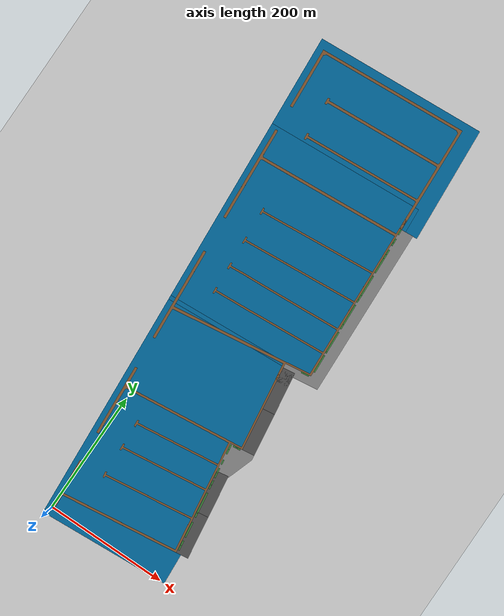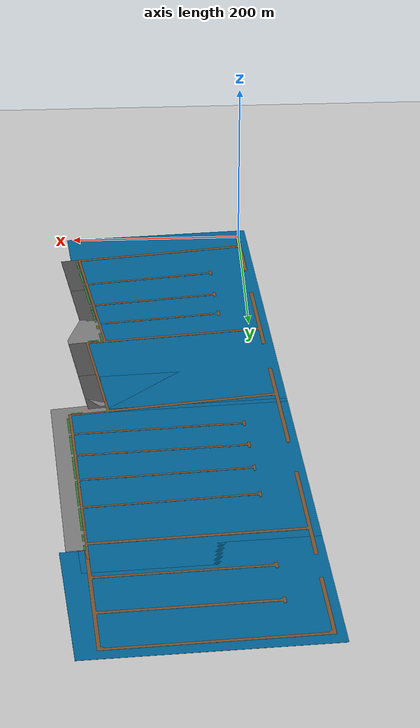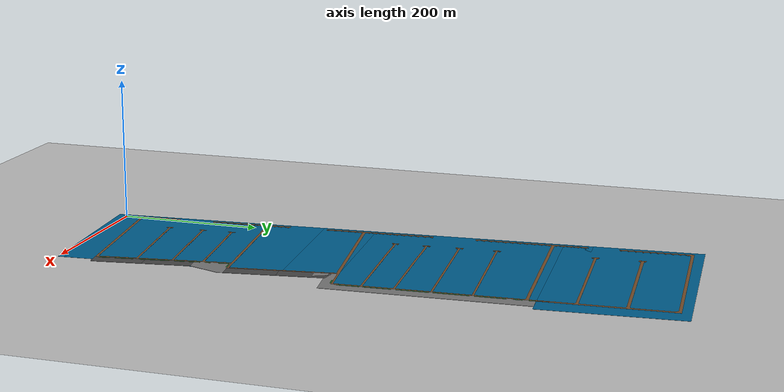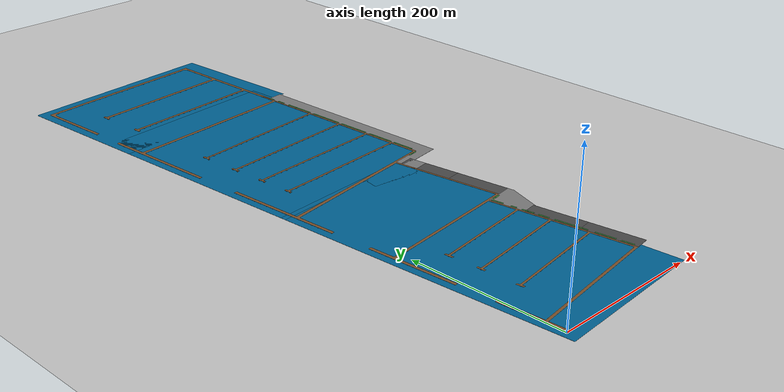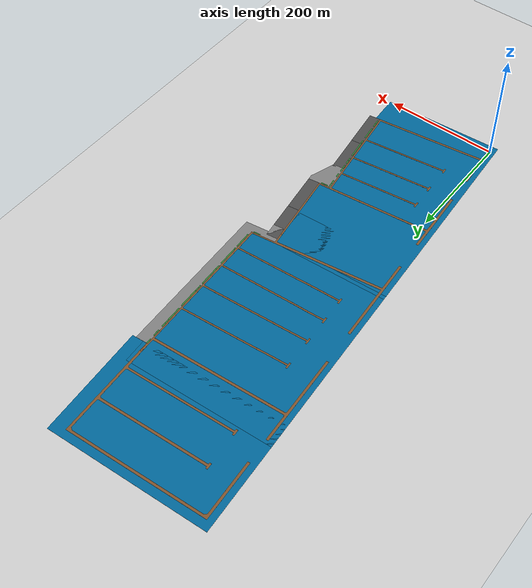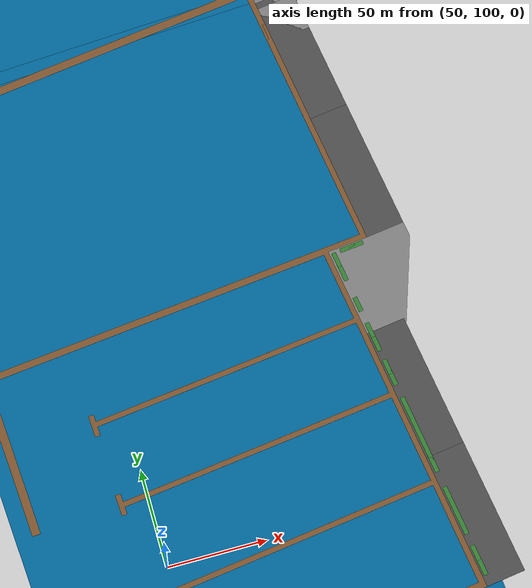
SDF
<sdf version="1.7">
 <world name="marina_base">
  <plugin name="gazebo_ros_state" filename="libgazebo_ros_state.so">
   <ros><namespace>/gazebo</namespace></ros>
   <update_rate>1.0</update_rate>
  </plugin>
  <light name="sun" type="directional">
   <pose>0 0 10 0 -0 0</pose>
   <diffuse>0.8 0.8 0.8 1</diffuse>
   <specular>0.2 0.2 0.2 1</specular>
   <attenuation>
    <range>1000</range>
    <constant>0.9</constant>
    <linear>0.01</linear>
    <quadratic>0.001</quadratic>
   </attenuation>
   <direction>-0.5 0.1 -0.9</direction>
   <spot><inner_angle>0</inner_angle><outer_angle>0</outer_angle><falloff>0</falloff></spot>
  </light>
  <model name="ground_plane">
   <pose>50 50 -1 0 -0 0</pose>
   <static>1</static>
   <link name="link">
    <collision name="collision">
     <geometry><plane><normal>0 0 1</normal><size>100 100</size></plane></geometry>
     <surface><friction><ode><mu>100</mu><mu2>50</mu2></ode></friction></surface>
    </collision>
    <visual name="visual">
     <cast_shadows>0</cast_shadows>
     <geometry><plane><normal>0 0 1</normal><size>100 100</size></plane></geometry>
     <material>
      <script><uri>file://media/materials/scripts/gazebo.material</uri><name>Gazebo/Grey</name></script>
     </material>
    </visual>
   </link>
  </model>
  <gravity>0 0 -9.8</gravity>
  <magnetic_field>6e-06 2.3e-05 -4.2e-05</magnetic_field>
  <atmosphere type="adiabatic"/>
  <physics type="ode">
   <max_step_size>0.001</max_step_size>
   <real_time_factor>1</real_time_factor>
   <real_time_update_rate>1000</real_time_update_rate>
  </physics>
  <scene><ambient>0.4 0.4 0.4 1</ambient><background>0.7 0.7 0.7 1</background><shadows>1</shadows></scene>
  <audio><device>default</device></audio>
  <spherical_coordinates>
   <surface_model>EARTH_WGS84</surface_model>
   <latitude_deg>45.0271</latitude_deg>
   <longitude_deg>14.6258</longitude_deg>
   <elevation>1.5</elevation>
   <heading_deg>180</heading_deg>
  </spherical_coordinates>
  <light name="sun_clone" type="directional">
   <pose>-7.81637 198.095 40 0 -0 0</pose>
   <diffuse>0.8 0.8 0.8 1</diffuse>
   <specular>0.2 0.2 0.2 1</specular>
   <direction>-0.483368 0.096674 -0.870063</direction>
   <attenuation>
    <range>1000</range>
    <constant>0.9</constant>
    <linear>0.01</linear>
    <quadratic>0.001</quadratic>
   </attenuation>
   <cast_shadows>0</cast_shadows>
   <spot><inner_angle>0</inner_angle><outer_angle>0</outer_angle><falloff>0</falloff></spot>
  </light>
  <model name="zone_A">
   <static>1</static>
   <pose>96.71 55.0214 0 0 -0 0.067998</pose>
   <frame name="Marina_Zona_A::__model__" attached_to="Marina_Zona_A::link">
    <pose relative_to="__model__">-100.225 -48.3232 0.08 0 -0 0</pose>
   </frame>
   <link name="Marina_Zona_A::link">
    <inertial>
     <mass>100000</mass>
     <inertia><ixx>0</ixx><ixy>0</ixy><ixz>0</ixz><iyy>0</iyy><iyz>0</iyz><izz>0</izz></inertia>
    </inertial>
    <pose relative_to="Marina_Zona_A::__model__">0 0 0 0 -0 0</pose>
    <visual name="visual">
     <geometry>
      <mesh>
       <uri>/marinero_simulations/models/Marina_Zona_A/meshes/Marina_Zona_A.stl</uri>
       <scale>1 1 1</scale>
      </mesh>
     </geometry>
     <material>
      <script><uri>file://media/materials/scripts/gazebo.material</uri><name>Gazebo/Brown</name></script>
      <ambient>0.278 0.129 0.02 1</ambient>
      <diffuse>0.278 0.129 0.02 1</diffuse>
      <specular>0.278 0.129 0.02 1</specular>
      <emissive>0 0 0 1</emissive>
      <shader type="pixel"><normal_map>__default__</normal_map></shader>
     </material>
    </visual>
    <collision name="collision">
     <geometry>
      <mesh>
       <uri>/marinero_simulations/models/Marina_Zona_A/meshes/Marina_Zona_A.stl</uri>
       <scale>1 1 1</scale>
      </mesh>
     </geometry>
     <surface>
      <friction>
       <ode><mu>1</mu><mu2>1</mu2><fdir1>0 0 0</fdir1><slip1>0.001</slip1><slip2>1e-05</slip2></ode>
       <torsional>
        <coefficient>1</coefficient>
        <patch_radius>0</patch_radius>
        <surface_radius>0</surface_radius>
        <use_patch_radius>1</use_patch_radius>
        <ode><slip>0</slip></ode>
       </torsional>
      </friction>
      <bounce><restitution_coefficient>0</restitution_coefficient><threshold>1000</threshold></bounce>
      <contact>
       <collide_without_contact>0</collide_without_contact>
       <collide_without_contact_bitmask>0</collide_without_contact_bitmask>
       <collide_bitmask>1</collide_bitmask>
       <ode>
        <soft_cfm>0</soft_cfm>
        <soft_erp>0.2</soft_erp>
        <kp>1e+13</kp>
        <kd>10</kd>
        <max_vel>0.01</max_vel>
        <min_depth>0.001</min_depth>
       </ode>
       <bullet>
        <split_impulse>1</split_impulse>
        <split_impulse_penetration_threshold>-0.01</split_impulse_penetration_threshold>
        <soft_cfm>0</soft_cfm>
        <soft_erp>0.2</soft_erp>
        <kp>1e+11</kp>
        <kd>100</kd>
       </bullet>
      </contact>
     </surface>
    </collision>
   </link>
   <static>1</static>
   <frame name="sea_plane_A::__model__" attached_to="sea_plane_A::link">
    <pose relative_to="__model__">-1.12 126.455 0 0 -0 0</pose>
   </frame>
   <link name="sea_plane_A::link">
    <pose relative_to="sea_plane_A::__model__">0 0 0 0 -0 0</pose>
    <inertial>
     <mass>5.27875e+06</mass>
     <inertia>
      <ixx>4.66688e+09</ixx>
      <ixy>0</ixy>
      <ixz>0</ixz>
      <iyy>1.84866e+10</iyy>
      <iyz>0</iyz>
      <izz>2.31535e+10</izz>
     </inertia>
    </inertial>
    <visual name="visual">
     <cast_shadows>0</cast_shadows>
     <geometry><box><size>215 378 0.25</size></box></geometry>
     <material>
      <script>
       <uri>model://sea_plane/materials/scripts</uri>
       <uri>model://sea_plane/materials/textures</uri>
       <name>vrc/sea</name>
      </script>
      <shader type="pixel"><normal_map>__default__</normal_map></shader>
      <ambient>0 0.4 0.6 0</ambient>
      <diffuse>0 0.4 0.6 1</diffuse>
      <specular>0.2 0.2 0.2 1</specular>
      <emissive>0 0 0 1</emissive>
     </material>
    </visual>
    <collision name="collision">
     <geometry><box><size>215 378 0.25</size></box></geometry>
     <surface>
      <friction>
       <ode><mu>1</mu><mu2>1</mu2><fdir1>0 0 0</fdir1><slip1>0</slip1><slip2>0</slip2></ode>
       <torsional>
        <coefficient>1</coefficient>
        <patch_radius>0</patch_radius>
        <surface_radius>0</surface_radius>
        <use_patch_radius>1</use_patch_radius>
        <ode><slip>0</slip></ode>
       </torsional>
      </friction>
      <bounce><restitution_coefficient>0</restitution_coefficient><threshold>1e+06</threshold></bounce>
      <contact>
       <collide_without_contact>0</collide_without_contact>
       <collide_without_contact_bitmask>1</collide_without_contact_bitmask>
       <collide_bitmask>1</collide_bitmask>
       <ode>
        <soft_cfm>0</soft_cfm>
        <soft_erp>0.2</soft_erp>
        <kp>1e+13</kp>
        <kd>1</kd>
        <max_vel>0.01</max_vel>
        <min_depth>0</min_depth>
       </ode>
       <bullet>
        <split_impulse>1</split_impulse>
        <split_impulse_penetration_threshold>-0.01</split_impulse_penetration_threshold>
        <soft_cfm>0</soft_cfm>
        <soft_erp>0.2</soft_erp>
        <kp>1e+13</kp>
        <kd>1</kd>
       </bullet>
      </contact>
     </surface>
    </collision>
   </link>
   <static>1</static>
   <frame name="asphalt_plane_0::__model__" attached_to="asphalt_plane_0::link">
    <pose relative_to="__model__">105.657 22.9966 0 0 0 -1.498</pose>
   </frame>
   <link name="asphalt_plane_0::link">
    <pose relative_to="asphalt_plane_0::__model__">0 0 1.015 0 -0 0</pose>
    <inertial>
     <mass>1</mass>
     <inertia><ixx>1</ixx><ixy>0</ixy><ixz>0</ixz><iyy>1</iyy><iyz>0</iyz><izz>1</izz></inertia>
    </inertial>
    <visual name="visual">
     <cast_shadows>0</cast_shadows>
     <geometry><box><size>70 20 0.5</size></box></geometry>
     <material>
      <script>
       <uri>model://asphalt_plane/materials/scripts</uri>
       <uri>model://asphalt_plane/materials/textures</uri>
       <name>vrc/asphalt</name>
      </script>
      <shader type="pixel"><normal_map>__default__</normal_map></shader>
      <ambient>0.5 0.5 0.5 1</ambient>
      <diffuse>0.5 0.5 0.5 1</diffuse>
      <specular>0.2 0.2 0.2 1</specular>
      <emissive>0 0 0 1</emissive>
     </material>
    </visual>
    <collision name="collision">
     <geometry><box><size>70 20 0.5</size></box></geometry>
     <surface>
      <friction>
       <ode><mu>1</mu><mu2>1</mu2><fdir1>0 0 0</fdir1><slip1>0.001</slip1><slip2>1e-05</slip2></ode>
       <torsional>
        <coefficient>1</coefficient>
        <patch_radius>0</patch_radius>
        <surface_radius>0</surface_radius>
        <use_patch_radius>1</use_patch_radius>
        <ode><slip>0</slip></ode>
       </torsional>
      </friction>
      <bounce><restitution_coefficient>0</restitution_coefficient><threshold>1e+06</threshold></bounce>
      <contact>
       <collide_without_contact>0</collide_without_contact>
       <collide_without_contact_bitmask>1</collide_without_contact_bitmask>
       <collide_bitmask>1</collide_bitmask>
       <ode>
        <soft_cfm>0</soft_cfm>
        <soft_erp>0.2</soft_erp>
        <kp>1e+13</kp>
        <kd>1</kd>
        <max_vel>0.01</max_vel>
        <min_depth>0</min_depth>
       </ode>
       <bullet>
        <split_impulse>1</split_impulse>
        <split_impulse_penetration_threshold>-0.01</split_impulse_penetration_threshold>
        <soft_cfm>0</soft_cfm>
        <soft_erp>0.2</soft_erp>
        <kp>1e+13</kp>
        <kd>1</kd>
       </bullet>
      </contact>
     </surface>
    </collision>
   </link>
   <static>1</static>
   <frame name="asphalt_plane_1::__model__" attached_to="asphalt_plane_1::link">
    <pose relative_to="__model__">100.593 92.427 0 0 0 -1.498</pose>
   </frame>
   <link name="asphalt_plane_1::link">
    <pose relative_to="asphalt_plane_1::__model__">0 0 1.015 0 -0 0</pose>
    <inertial>
     <mass>1</mass>
     <inertia><ixx>1</ixx><ixy>0</ixy><ixz>0</ixz><iyy>1</iyy><iyz>0</iyz><izz>1</izz></inertia>
    </inertial>
    <visual name="visual">
     <cast_shadows>0</cast_shadows>
     <geometry><box><size>70 20 0.5</size></box></geometry>
     <material>
      <script>
       <uri>model://asphalt_plane/materials/scripts</uri>
       <uri>model://asphalt_plane/materials/textures</uri>
       <name>vrc/asphalt</name>
      </script>
      <shader type="pixel"><normal_map>__default__</normal_map></shader>
      <ambient>0.5 0.5 0.5 1</ambient>
      <diffuse>0.5 0.5 0.5 1</diffuse>
      <specular>0.2 0.2 0.2 1</specular>
      <emissive>0 0 0 1</emissive>
     </material>
    </visual>
    <collision name="collision">
     <geometry><box><size>70 20 0.5</size></box></geometry>
     <surface>
      <friction>
       <ode><mu>1</mu><mu2>1</mu2><fdir1>0 0 0</fdir1><slip1>0.001</slip1><slip2>1e-05</slip2></ode>
       <torsional>
        <coefficient>1</coefficient>
        <patch_radius>0</patch_radius>
        <surface_radius>0</surface_radius>
        <use_patch_radius>1</use_patch_radius>
        <ode><slip>0</slip></ode>
       </torsional>
      </friction>
      <bounce><restitution_coefficient>0</restitution_coefficient><threshold>1e+06</threshold></bounce>
      <contact>
       <collide_without_contact>0</collide_without_contact>
       <collide_without_contact_bitmask>1</collide_without_contact_bitmask>
       <collide_bitmask>1</collide_bitmask>
       <ode>
        <soft_cfm>0</soft_cfm>
        <soft_erp>0.2</soft_erp>
        <kp>1e+13</kp>
        <kd>1</kd>
        <max_vel>0.01</max_vel>
        <min_depth>0</min_depth>
       </ode>
       <bullet>
        <split_impulse>1</split_impulse>
        <split_impulse_penetration_threshold>-0.01</split_impulse_penetration_threshold>
        <soft_cfm>0</soft_cfm>
        <soft_erp>0.2</soft_erp>
        <kp>1e+13</kp>
        <kd>1</kd>
       </bullet>
      </contact>
     </surface>
    </collision>
   </link>
   <static>1</static>
   <frame name="asphalt_plane_angle_section::__model__" attached_to="asphalt_plane_angle_section::link">
    <pose relative_to="__model__">96.4113 149.332 0 0 -0 0</pose>
   </frame>
   <link name="asphalt_plane_angle_section::link">
    <inertial>
     <mass>1</mass>
     <inertia><ixx>1</ixx><ixy>0</ixy><ixz>0</ixz><iyy>1</iyy><iyz>0</iyz><izz>1</izz></inertia>
    </inertial>
    <pose relative_to="asphalt_plane_angle_section::__model__">0 0 1.015 0 0 -1.4967</pose>
    <visual name="visual">
     <geometry>
      <mesh>
       <uri>/marinero_simulations/models/asphalt_plane_angle_section/meshes/asphalt_plane_angle_section.dae</uri>
       <scale>1 1 5</scale>
      </mesh>
     </geometry>
     <material>
      <script>
       <uri>/marinero_simulations/models/asphalt_plane_angle_section/materials/scripts</uri>
       <uri>/marinero_simulations/models/asphalt_plane_angle_section/materials/textures/tarmac.png</uri>
       <name>asphalt/texture</name>
      </script>
      <shader type="pixel"><normal_map>__default__</normal_map></shader>
      <ambient>0.5 0.5 0.5 1</ambient>
      <diffuse>0.5 0.5 0.5 1</diffuse>
      <specular>0.2 0.2 0.2 1</specular>
      <emissive>0 0 0 1</emissive>
     </material>
    </visual>
    <collision name="collision">
     <geometry>
      <mesh>
       <uri>/marinero_simulations/models/asphalt_plane_angle_section/meshes/asphalt_plane_angle_section.dae</uri>
       <scale>1 1 5</scale>
      </mesh>
     </geometry>
     <surface>
      <friction>
       <ode><mu>1</mu><mu2>1</mu2><fdir1>0 0 0</fdir1><slip1>0.001</slip1><slip2>1e-05</slip2></ode>
       <torsional>
        <coefficient>1</coefficient>
        <patch_radius>0</patch_radius>
        <surface_radius>0</surface_radius>
        <use_patch_radius>1</use_patch_radius>
        <ode><slip>0</slip></ode>
       </torsional>
      </friction>
      <bounce><restitution_coefficient>0</restitution_coefficient><threshold>1e+06</threshold></bounce>
      <contact>
       <collide_without_contact>0</collide_without_contact>
       <collide_without_contact_bitmask>1</collide_without_contact_bitmask>
       <collide_bitmask>1</collide_bitmask>
       <ode>
        <soft_cfm>0</soft_cfm>
        <soft_erp>0.2</soft_erp>
        <kp>1e+13</kp>
        <kd>1</kd>
        <max_vel>0.01</max_vel>
        <min_depth>0</min_depth>
       </ode>
       <bullet>
        <split_impulse>1</split_impulse>
        <split_impulse_penetration_threshold>-0.01</split_impulse_penetration_threshold>
        <soft_cfm>0</soft_cfm>
        <soft_erp>0.2</soft_erp>
        <kp>1e+13</kp>
        <kd>1</kd>
       </bullet>
      </contact>
     </surface>
    </collision>
   </link>
   <static>1</static>
   <frame name="asphalt_plane_2::__model__" attached_to="asphalt_plane_2::link">
    <pose relative_to="__model__">113.068 209.915 0 0 0 -1.5</pose>
   </frame>
   <link name="asphalt_plane_2::link">
    <pose relative_to="asphalt_plane_2::__model__">0 0 1.015 0 -0 0</pose>
    <inertial>
     <mass>1</mass>
     <inertia><ixx>1</ixx><ixy>0</ixy><ixz>0</ixz><iyy>1</iyy><iyz>0</iyz><izz>1</izz></inertia>
    </inertial>
    <visual name="visual">
     <cast_shadows>0</cast_shadows>
     <geometry><box><size>70 20 0.5</size></box></geometry>
     <material>
      <script>
       <uri>model://asphalt_plane/materials/scripts</uri>
       <uri>model://asphalt_plane/materials/textures</uri>
       <name>vrc/asphalt</name>
      </script>
      <shader type="pixel"><normal_map>__default__</normal_map></shader>
      <ambient>0.5 0.5 0.5 1</ambient>
      <diffuse>0.5 0.5 0.5 1</diffuse>
      <specular>0.2 0.2 0.2 1</specular>
      <emissive>0 0 0 1</emissive>
     </material>
    </visual>
    <collision name="collision">
     <geometry><box><size>70 20 0.5</size></box></geometry>
     <surface>
      <friction>
       <ode><mu>1</mu><mu2>1</mu2><fdir1>0 0 0</fdir1><slip1>0.001</slip1><slip2>1e-05</slip2></ode>
       <torsional>
        <coefficient>1</coefficient>
        <patch_radius>0</patch_radius>
        <surface_radius>0</surface_radius>
        <use_patch_radius>1</use_patch_radius>
        <ode><slip>0</slip></ode>
       </torsional>
      </friction>
      <bounce><restitution_coefficient>0</restitution_coefficient><threshold>1e+06</threshold></bounce>
      <contact>
       <collide_without_contact>0</collide_without_contact>
       <collide_without_contact_bitmask>1</collide_without_contact_bitmask>
       <collide_bitmask>1</collide_bitmask>
       <ode>
        <soft_cfm>0</soft_cfm>
        <soft_erp>0.2</soft_erp>
        <kp>1e+13</kp>
        <kd>1</kd>
        <max_vel>0.01</max_vel>
        <min_depth>0</min_depth>
       </ode>
       <bullet>
        <split_impulse>1</split_impulse>
        <split_impulse_penetration_threshold>-0.01</split_impulse_penetration_threshold>
        <soft_cfm>0</soft_cfm>
        <soft_erp>0.2</soft_erp>
        <kp>1e+13</kp>
        <kd>1</kd>
       </bullet>
      </contact>
     </surface>
    </collision>
   </link>
   <static>1</static>
   <frame name="asphalt_plane_3::__model__" attached_to="asphalt_plane_3::link">
    <pose relative_to="__model__">108.119 279.695 0 0 0 -1.5</pose>
   </frame>
   <link name="asphalt_plane_3::link">
    <pose relative_to="asphalt_plane_3::__model__">0 0 1.015 0 -0 0</pose>
    <inertial>
     <mass>1</mass>
     <inertia><ixx>1</ixx><ixy>0</ixy><ixz>0</ixz><iyy>1</iyy><iyz>0</iyz><izz>1</izz></inertia>
    </inertial>
    <visual name="visual">
     <cast_shadows>0</cast_shadows>
     <geometry><box><size>70 20 0.5</size></box></geometry>
     <material>
      <script>
       <uri>model://asphalt_plane/materials/scripts</uri>
       <uri>model://asphalt_plane/materials/textures</uri>
       <name>vrc/asphalt</name>
      </script>
      <shader type="pixel"><normal_map>__default__</normal_map></shader>
      <ambient>0.5 0.5 0.5 1</ambient>
      <diffuse>0.5 0.5 0.5 1</diffuse>
      <specular>0.2 0.2 0.2 1</specular>
      <emissive>0 0 0 1</emissive>
     </material>
    </visual>
    <collision name="collision">
     <geometry><box><size>70 20 0.5</size></box></geometry>
     <surface>
      <friction>
       <ode><mu>1</mu><mu2>1</mu2><fdir1>0 0 0</fdir1><slip1>0.001</slip1><slip2>1e-05</slip2></ode>
       <torsional>
        <coefficient>1</coefficient>
        <patch_radius>0</patch_radius>
        <surface_radius>0</surface_radius>
        <use_patch_radius>1</use_patch_radius>
        <ode><slip>0</slip></ode>
       </torsional>
      </friction>
      <bounce><restitution_coefficient>0</restitution_coefficient><threshold>1e+06</threshold></bounce>
      <contact>
       <collide_without_contact>0</collide_without_contact>
       <collide_without_contact_bitmask>1</collide_without_contact_bitmask>
       <collide_bitmask>1</collide_bitmask>
       <ode>
        <soft_cfm>0</soft_cfm>
        <soft_erp>0.2</soft_erp>
        <kp>1e+13</kp>
        <kd>1</kd>
        <max_vel>0.01</max_vel>
        <min_depth>0</min_depth>
       </ode>
       <bullet>
        <split_impulse>1</split_impulse>
        <split_impulse_penetration_threshold>-0.01</split_impulse_penetration_threshold>
        <soft_cfm>0</soft_cfm>
        <soft_erp>0.2</soft_erp>
        <kp>1e+13</kp>
        <kd>1</kd>
       </bullet>
      </contact>
     </surface>
    </collision>
   </link>
   <static>1</static>
   <frame name="grass_0::__model__" attached_to="grass_0::link">
    <pose relative_to="__model__">99.5246 -3.1658 0 0 -0 0.0925</pose>
   </frame>
   <link name="grass_0::link">
    <pose relative_to="grass_0::__model__">0 0 1.255 0 0 -1.5905</pose>
    <inertial>
     <mass>1</mass>
     <inertia><ixx>1</ixx><ixy>0</ixy><ixz>0</ixz><iyy>1</iyy><iyz>0</iyz><izz>1</izz></inertia>
    </inertial>
    <visual name="visual">
     <cast_shadows>0</cast_shadows>
     <geometry><box><size>8 2.25 0.1</size></box></geometry>
     <material>
      <script>
       <uri>/marinero_simulations/models/grass_plane_SM/materials/scripts</uri>
       <uri>/marinero_simulations/models/grass_plane_SM/materials/textures/grass.jpg</uri>
       <name>grass_SM/texture</name>
      </script>
      <shader type="pixel"><normal_map>__default__</normal_map></shader>
      <ambient>0.2 0.5 0.2 1</ambient>
      <diffuse>0.2 0.5 0.2 1</diffuse>
      <specular>0.2 0.2 0.2 1</specular>
      <emissive>0 0 0 1</emissive>
     </material>
    </visual>
    <collision name="collision">
     <geometry><box><size>8 2.25 0.1</size></box></geometry>
     <surface>
      <friction>
       <ode><mu>1</mu><mu2>1</mu2><fdir1>0 0 0</fdir1><slip1>0.001</slip1><slip2>1e-05</slip2></ode>
       <torsional>
        <coefficient>1</coefficient>
        <patch_radius>0</patch_radius>
        <surface_radius>0</surface_radius>
        <use_patch_radius>1</use_patch_radius>
        <ode><slip>0</slip></ode>
       </torsional>
      </friction>
      <bounce><restitution_coefficient>0</restitution_coefficient><threshold>1e+06</threshold></bounce>
      <contact>
       <collide_without_contact>0</collide_without_contact>
       <collide_without_contact_bitmask>1</collide_without_contact_bitmask>
       <collide_bitmask>1</collide_bitmask>
       <ode>
        <soft_cfm>0</soft_cfm>
        <soft_erp>0.2</soft_erp>
        <kp>1e+13</kp>
        <kd>1</kd>
        <max_vel>0.01</max_vel>
        <min_depth>0</min_depth>
       </ode>
       <bullet>
        <split_impulse>1</split_impulse>
        <split_impulse_penetration_threshold>-0.01</split_impulse_penetration_threshold>
        <soft_cfm>0</soft_cfm>
        <soft_erp>0.2</soft_erp>
        <kp>1e+13</kp>
        <kd>1</kd>
       </bullet>
      </contact>
     </surface>
    </collision>
   </link>
   <static>1</static>
   <frame name="grass_1::__model__" attached_to="grass_1::link">
    <pose relative_to="__model__">98.95 4.71188 0 0 -0 0.0925</pose>
   </frame>
   <link name="grass_1::link">
    <pose relative_to="grass_1::__model__">0 0 1.255 0 0 -1.5905</pose>
    <inertial>
     <mass>1</mass>
     <inertia><ixx>1</ixx><ixy>0</ixy><ixz>0</ixz><iyy>1</iyy><iyz>0</iyz><izz>1</izz></inertia>
    </inertial>
    <visual name="visual">
     <cast_shadows>0</cast_shadows>
     <geometry><box><size>8 2.25 0.1</size></box></geometry>
     <material>
      <script>
       <uri>/marinero_simulations/models/grass_plane_SM/materials/scripts</uri>
       <uri>/marinero_simulations/models/grass_plane_SM/materials/textures/grass.jpg</uri>
       <name>grass_SM/texture</name>
      </script>
      <shader type="pixel"><normal_map>__default__</normal_map></shader>
      <ambient>0.2 0.5 0.2 1</ambient>
      <diffuse>0.2 0.5 0.2 1</diffuse>
      <specular>0.2 0.2 0.2 1</specular>
      <emissive>0 0 0 1</emissive>
     </material>
    </visual>
    <collision name="collision">
     <geometry><box><size>8 2.25 0.1</size></box></geometry>
     <surface>
      <friction>
       <ode><mu>1</mu><mu2>1</mu2><fdir1>0 0 0</fdir1><slip1>0.001</slip1><slip2>1e-05</slip2></ode>
       <torsional>
        <coefficient>1</coefficient>
        <patch_radius>0</patch_radius>
        <surface_radius>0</surface_radius>
        <use_patch_radius>1</use_patch_radius>
        <ode><slip>0</slip></ode>
       </torsional>
      </friction>
      <bounce><restitution_coefficient>0</restitution_coefficient><threshold>1e+06</threshold></bounce>
      <contact>
       <collide_without_contact>0</collide_without_contact>
       <collide_without_contact_bitmask>1</collide_without_contact_bitmask>
       <collide_bitmask>1</collide_bitmask>
       <ode>
        <soft_cfm>0</soft_cfm>
        <soft_erp>0.2</soft_erp>
        <kp>1e+13</kp>
        <kd>1</kd>
        <max_vel>0.01</max_vel>
        <min_depth>0</min_depth>
       </ode>
       <bullet>
        <split_impulse>1</split_impulse>
        <split_impulse_penetration_threshold>-0.01</split_impulse_penetration_threshold>
        <soft_cfm>0</soft_cfm>
        <soft_erp>0.2</soft_erp>
        <kp>1e+13</kp>
        <kd>1</kd>
       </bullet>
      </contact>
     </surface>
    </collision>
   </link>
   <static>1</static>
   <frame name="grass_2::__model__" attached_to="grass_2::link">
    <pose relative_to="__model__">97.35 27.6528 0 0 -0 0.0925</pose>
   </frame>
   <link name="grass_2::link">
    <pose relative_to="grass_2::__model__">0 0 1.255 0 0 -1.5905</pose>
    <inertial>
     <mass>1</mass>
     <inertia><ixx>1</ixx><ixy>0</ixy><ixz>0</ixz><iyy>1</iyy><iyz>0</iyz><izz>1</izz></inertia>
    </inertial>
    <visual name="visual">
     <cast_shadows>0</cast_shadows>
     <geometry><box><size>25.75 2.25 0.1</size></box></geometry>
     <material>
      <script>
       <uri>/marinero_simulations/models/grass_plane_M/materials/scripts</uri>
       <uri>/marinero_simulations/models/grass_plane_M/materials/textures/grass.jpg</uri>
       <name>grass_M/texture</name>
      </script>
      <shader type="pixel"><normal_map>__default__</normal_map></shader>
      <ambient>0.2 0.5 0.2 1</ambient>
      <diffuse>0.2 0.5 0.2 1</diffuse>
      <specular>0.2 0.2 0.2 1</specular>
      <emissive>0 0 0 1</emissive>
     </material>
    </visual>
    <collision name="collision">
     <geometry><box><size>25.75 2.25 0.1</size></box></geometry>
     <surface>
      <friction>
       <ode><mu>1</mu><mu2>1</mu2><fdir1>0 0 0</fdir1><slip1>0.001</slip1><slip2>1e-05</slip2></ode>
       <torsional>
        <coefficient>1</coefficient>
        <patch_radius>0</patch_radius>
        <surface_radius>0</surface_radius>
        <use_patch_radius>1</use_patch_radius>
        <ode><slip>0</slip></ode>
       </torsional>
      </friction>
      <bounce><restitution_coefficient>0</restitution_coefficient><threshold>1e+06</threshold></bounce>
      <contact>
       <collide_without_contact>0</collide_without_contact>
       <collide_without_contact_bitmask>1</collide_without_contact_bitmask>
       <collide_bitmask>1</collide_bitmask>
       <ode>
        <soft_cfm>0</soft_cfm>
        <soft_erp>0.2</soft_erp>
        <kp>1e+13</kp>
        <kd>1</kd>
        <max_vel>0.01</max_vel>
        <min_depth>0</min_depth>
       </ode>
       <bullet>
        <split_impulse>1</split_impulse>
        <split_impulse_penetration_threshold>-0.01</split_impulse_penetration_threshold>
        <soft_cfm>0</soft_cfm>
        <soft_erp>0.2</soft_erp>
        <kp>1e+13</kp>
        <kd>1</kd>
       </bullet>
      </contact>
     </surface>
    </collision>
   </link>
   <static>1</static>
   <frame name="grass_3::__model__" attached_to="grass_3::link">
    <pose relative_to="__model__">95.6044 52.7577 0 0 -0 0.0925</pose>
   </frame>
   <link name="grass_3::link">
    <pose relative_to="grass_3::__model__">0 0 1.255 0 0 -1.5905</pose>
    <inertial>
     <mass>1</mass>
     <inertia><ixx>1</ixx><ixy>0</ixy><ixz>0</ixz><iyy>1</iyy><iyz>0</iyz><izz>1</izz></inertia>
    </inertial>
    <visual name="visual">
     <cast_shadows>0</cast_shadows>
     <geometry><box><size>8 2.25 0.1</size></box></geometry>
     <material>
      <script>
       <uri>/marinero_simulations/models/grass_plane_SM/materials/scripts</uri>
       <uri>/marinero_simulations/models/grass_plane_SM/materials/textures/grass.jpg</uri>
       <name>grass_SM/texture</name>
      </script>
      <shader type="pixel"><normal_map>__default__</normal_map></shader>
      <ambient>0.2 0.5 0.2 1</ambient>
      <diffuse>0.2 0.5 0.2 1</diffuse>
      <specular>0.2 0.2 0.2 1</specular>
      <emissive>0 0 0 1</emissive>
     </material>
    </visual>
    <collision name="collision">
     <geometry><box><size>8 2.25 0.1</size></box></geometry>
     <surface>
      <friction>
       <ode><mu>1</mu><mu2>1</mu2><fdir1>0 0 0</fdir1><slip1>0.001</slip1><slip2>1e-05</slip2></ode>
       <torsional>
        <coefficient>1</coefficient>
        <patch_radius>0</patch_radius>
        <surface_radius>0</surface_radius>
        <use_patch_radius>1</use_patch_radius>
        <ode><slip>0</slip></ode>
       </torsional>
      </friction>
      <bounce><restitution_coefficient>0</restitution_coefficient><threshold>1e+06</threshold></bounce>
      <contact>
       <collide_without_contact>0</collide_without_contact>
       <collide_without_contact_bitmask>1</collide_without_contact_bitmask>
       <collide_bitmask>1</collide_bitmask>
       <ode>
        <soft_cfm>0</soft_cfm>
        <soft_erp>0.2</soft_erp>
        <kp>1e+13</kp>
        <kd>1</kd>
        <max_vel>0.01</max_vel>
        <min_depth>0</min_depth>
       </ode>
       <bullet>
        <split_impulse>1</split_impulse>
        <split_impulse_penetration_threshold>-0.01</split_impulse_penetration_threshold>
        <soft_cfm>0</soft_cfm>
        <soft_erp>0.2</soft_erp>
        <kp>1e+13</kp>
        <kd>1</kd>
       </bullet>
      </contact>
     </surface>
    </collision>
   </link>
   <static>1</static>
   <frame name="grass_4::__model__" attached_to="grass_4::link">
    <pose relative_to="__model__">94.16 72.5637 0 0 -0 0.0925</pose>
   </frame>
   <link name="grass_4::link">
    <pose relative_to="grass_4::__model__">0 0 1.255 0 0 -1.5905</pose>
    <inertial>
     <mass>1</mass>
     <inertia><ixx>1</ixx><ixy>0</ixy><ixz>0</ixz><iyy>1</iyy><iyz>0</iyz><izz>1</izz></inertia>
    </inertial>
    <visual name="visual">
     <cast_shadows>0</cast_shadows>
     <geometry><box><size>35 2.25 0.1</size></box></geometry>
     <material>
      <script>
       <uri>model://grass_plane/materials/scripts</uri>
       <uri>model://grass_plane/materials/textures/grass.jpg</uri>
       <name>grass/texture</name>
      </script>
      <shader type="pixel"><normal_map>__default__</normal_map></shader>
      <ambient>0.2 0.5 0.2 1</ambient>
      <diffuse>0.2 0.5 0.2 1</diffuse>
      <specular>0.2 0.2 0.2 1</specular>
      <emissive>0 0 0 1</emissive>
     </material>
    </visual>
    <collision name="collision">
     <geometry><box><size>35 2.25 0.1</size></box></geometry>
     <surface>
      <friction>
       <ode><mu>1</mu><mu2>1</mu2><fdir1>0 0 0</fdir1><slip1>0.001</slip1><slip2>1e-05</slip2></ode>
       <torsional>
        <coefficient>1</coefficient>
        <patch_radius>0</patch_radius>
        <surface_radius>0</surface_radius>
        <use_patch_radius>1</use_patch_radius>
        <ode><slip>0</slip></ode>
       </torsional>
      </friction>
      <bounce><restitution_coefficient>0</restitution_coefficient><threshold>1e+06</threshold></bounce>
      <contact>
       <collide_without_contact>0</collide_without_contact>
       <collide_without_contact_bitmask>1</collide_without_contact_bitmask>
       <collide_bitmask>1</collide_bitmask>
       <ode>
        <soft_cfm>0</soft_cfm>
        <soft_erp>0.2</soft_erp>
        <kp>1e+13</kp>
        <kd>1</kd>
        <max_vel>0.01</max_vel>
        <min_depth>0</min_depth>
       </ode>
       <bullet>
        <split_impulse>1</split_impulse>
        <split_impulse_penetration_threshold>-0.01</split_impulse_penetration_threshold>
        <soft_cfm>0</soft_cfm>
        <soft_erp>0.2</soft_erp>
        <kp>1e+13</kp>
        <kd>1</kd>
       </bullet>
      </contact>
     </surface>
    </collision>
   </link>
   <static>1</static>
   <frame name="grass_5::__model__" attached_to="grass_5::link">
    <pose relative_to="__model__">92.0607 100.811 0 0 -0 0.0925</pose>
   </frame>
   <link name="grass_5::link">
    <pose relative_to="grass_5::__model__">0 0 1.255 0 0 -1.5905</pose>
    <inertial>
     <mass>1</mass>
     <inertia><ixx>1</ixx><ixy>0</ixy><ixz>0</ixz><iyy>1</iyy><iyz>0</iyz><izz>1</izz></inertia>
    </inertial>
    <visual name="visual">
     <cast_shadows>0</cast_shadows>
     <geometry><box><size>8 2.25 0.1</size></box></geometry>
     <material>
      <script>
       <uri>/marinero_simulations/models/grass_plane_SM/materials/scripts</uri>
       <uri>/marinero_simulations/models/grass_plane_SM/materials/textures/grass.jpg</uri>
       <name>grass_SM/texture</name>
      </script>
      <shader type="pixel"><normal_map>__default__</normal_map></shader>
      <ambient>0.2 0.5 0.2 1</ambient>
      <diffuse>0.2 0.5 0.2 1</diffuse>
      <specular>0.2 0.2 0.2 1</specular>
      <emissive>0 0 0 1</emissive>
     </material>
    </visual>
    <collision name="collision">
     <geometry><box><size>8 2.25 0.1</size></box></geometry>
     <surface>
      <friction>
       <ode><mu>1</mu><mu2>1</mu2><fdir1>0 0 0</fdir1><slip1>0.001</slip1><slip2>1e-05</slip2></ode>
       <torsional>
        <coefficient>1</coefficient>
        <patch_radius>0</patch_radius>
        <surface_radius>0</surface_radius>
        <use_patch_radius>1</use_patch_radius>
        <ode><slip>0</slip></ode>
       </torsional>
      </friction>
      <bounce><restitution_coefficient>0</restitution_coefficient><threshold>1e+06</threshold></bounce>
      <contact>
       <collide_without_contact>0</collide_without_contact>
       <collide_without_contact_bitmask>1</collide_without_contact_bitmask>
       <collide_bitmask>1</collide_bitmask>
       <ode>
        <soft_cfm>0</soft_cfm>
        <soft_erp>0.2</soft_erp>
        <kp>1e+13</kp>
        <kd>1</kd>
        <max_vel>0.01</max_vel>
        <min_depth>0</min_depth>
       </ode>
       <bullet>
        <split_impulse>1</split_impulse>
        <split_impulse_penetration_threshold>-0.01</split_impulse_penetration_threshold>
        <soft_cfm>0</soft_cfm>
        <soft_erp>0.2</soft_erp>
        <kp>1e+13</kp>
        <kd>1</kd>
       </bullet>
      </contact>
     </surface>
    </collision>
   </link>
   <static>1</static>
   <frame name="grass_6::__model__" attached_to="grass_6::link">
    <pose relative_to="__model__">91.6 107.127 0 0 -0 0.0925</pose>
   </frame>
   <link name="grass_6::link">
    <pose relative_to="grass_6::__model__">0 0 1.255 0 0 -1.5905</pose>
    <inertial>
     <mass>1</mass>
     <inertia><ixx>1</ixx><ixy>0</ixy><ixz>0</ixz><iyy>1</iyy><iyz>0</iyz><izz>1</izz></inertia>
    </inertial>
    <visual name="visual">
     <cast_shadows>0</cast_shadows>
     <geometry><box><size>8 2.25 0.1</size></box></geometry>
     <material>
      <script>
       <uri>/marinero_simulations/models/grass_plane_SM/materials/scripts</uri>
       <uri>/marinero_simulations/models/grass_plane_SM/materials/textures/grass.jpg</uri>
       <name>grass_SM/texture</name>
      </script>
      <shader type="pixel"><normal_map>__default__</normal_map></shader>
      <ambient>0.2 0.5 0.2 1</ambient>
      <diffuse>0.2 0.5 0.2 1</diffuse>
      <specular>0.2 0.2 0.2 1</specular>
      <emissive>0 0 0 1</emissive>
     </material>
    </visual>
    <collision name="collision">
     <geometry><box><size>8 2.25 0.1</size></box></geometry>
     <surface>
      <friction>
       <ode><mu>1</mu><mu2>1</mu2><fdir1>0 0 0</fdir1><slip1>0.001</slip1><slip2>1e-05</slip2></ode>
       <torsional>
        <coefficient>1</coefficient>
        <patch_radius>0</patch_radius>
        <surface_radius>0</surface_radius>
        <use_patch_radius>1</use_patch_radius>
        <ode><slip>0</slip></ode>
       </torsional>
      </friction>
      <bounce><restitution_coefficient>0</restitution_coefficient><threshold>1e+06</threshold></bounce>
      <contact>
       <collide_without_contact>0</collide_without_contact>
       <collide_without_contact_bitmask>1</collide_without_contact_bitmask>
       <collide_bitmask>1</collide_bitmask>
       <ode>
        <soft_cfm>0</soft_cfm>
        <soft_erp>0.2</soft_erp>
        <kp>1e+13</kp>
        <kd>1</kd>
        <max_vel>0.01</max_vel>
        <min_depth>0</min_depth>
       </ode>
       <bullet>
        <split_impulse>1</split_impulse>
        <split_impulse_penetration_threshold>-0.01</split_impulse_penetration_threshold>
        <soft_cfm>0</soft_cfm>
        <soft_erp>0.2</soft_erp>
        <kp>1e+13</kp>
        <kd>1</kd>
       </bullet>
      </contact>
     </surface>
    </collision>
   </link>
   <static>1</static>
   <frame name="grass_7::__model__" attached_to="grass_7::link">
    <pose relative_to="__model__">90.676 120.106 0 0 -0 0.0925</pose>
   </frame>
   <link name="grass_7::link">
    <pose relative_to="grass_7::__model__">0 0 1.255 0 0 -1.5905</pose>
    <inertial>
     <mass>1</mass>
     <inertia><ixx>1</ixx><ixy>0</ixy><ixz>0</ixz><iyy>1</iyy><iyz>0</iyz><izz>1</izz></inertia>
    </inertial>
    <visual name="visual">
     <cast_shadows>0</cast_shadows>
     <geometry><box><size>8 2.25 0.1</size></box></geometry>
     <material>
      <script>
       <uri>/marinero_simulations/models/grass_plane_SM/materials/scripts</uri>
       <uri>/marinero_simulations/models/grass_plane_SM/materials/textures/grass.jpg</uri>
       <name>grass_SM/texture</name>
      </script>
      <shader type="pixel"><normal_map>__default__</normal_map></shader>
      <ambient>0.2 0.5 0.2 1</ambient>
      <diffuse>0.2 0.5 0.2 1</diffuse>
      <specular>0.2 0.2 0.2 1</specular>
      <emissive>0 0 0 1</emissive>
     </material>
    </visual>
    <collision name="collision">
     <geometry><box><size>8 2.25 0.1</size></box></geometry>
     <surface>
      <friction>
       <ode><mu>1</mu><mu2>1</mu2><fdir1>0 0 0</fdir1><slip1>0.001</slip1><slip2>1e-05</slip2></ode>
       <torsional>
        <coefficient>1</coefficient>
        <patch_radius>0</patch_radius>
        <surface_radius>0</surface_radius>
        <use_patch_radius>1</use_patch_radius>
        <ode><slip>0</slip></ode>
       </torsional>
      </friction>
      <bounce><restitution_coefficient>0</restitution_coefficient><threshold>1e+06</threshold></bounce>
      <contact>
       <collide_without_contact>0</collide_without_contact>
       <collide_without_contact_bitmask>1</collide_without_contact_bitmask>
       <collide_bitmask>1</collide_bitmask>
       <ode>
        <soft_cfm>0</soft_cfm>
        <soft_erp>0.2</soft_erp>
        <kp>1e+13</kp>
        <kd>1</kd>
        <max_vel>0.01</max_vel>
        <min_depth>0</min_depth>
       </ode>
       <bullet>
        <split_impulse>1</split_impulse>
        <split_impulse_penetration_threshold>-0.01</split_impulse_penetration_threshold>
        <soft_cfm>0</soft_cfm>
        <soft_erp>0.2</soft_erp>
        <kp>1e+13</kp>
        <kd>1</kd>
       </bullet>
      </contact>
     </surface>
    </collision>
   </link>
   <static>1</static>
   <frame name="grass_8::__model__" attached_to="grass_8::link">
    <pose relative_to="__model__">90.1 128.004 0 0 -0 0.0925</pose>
   </frame>
   <link name="grass_8::link">
    <pose relative_to="grass_8::__model__">0 0 1.255 0 0 -1.5905</pose>
    <inertial>
     <mass>1</mass>
     <inertia><ixx>1</ixx><ixy>0</ixy><ixz>0</ixz><iyy>1</iyy><iyz>0</iyz><izz>1</izz></inertia>
    </inertial>
    <visual name="visual">
     <cast_shadows>0</cast_shadows>
     <geometry><box><size>8 2.25 0.1</size></box></geometry>
     <material>
      <script>
       <uri>/marinero_simulations/models/grass_plane_SM/materials/scripts</uri>
       <uri>/marinero_simulations/models/grass_plane_SM/materials/textures/grass.jpg</uri>
       <name>grass_SM/texture</name>
      </script>
      <shader type="pixel"><normal_map>__default__</normal_map></shader>
      <ambient>0.2 0.5 0.2 1</ambient>
      <diffuse>0.2 0.5 0.2 1</diffuse>
      <specular>0.2 0.2 0.2 1</specular>
      <emissive>0 0 0 1</emissive>
     </material>
    </visual>
    <collision name="collision">
     <geometry><box><size>8 2.25 0.1</size></box></geometry>
     <surface>
      <friction>
       <ode><mu>1</mu><mu2>1</mu2><fdir1>0 0 0</fdir1><slip1>0.001</slip1><slip2>1e-05</slip2></ode>
       <torsional>
        <coefficient>1</coefficient>
        <patch_radius>0</patch_radius>
        <surface_radius>0</surface_radius>
        <use_patch_radius>1</use_patch_radius>
        <ode><slip>0</slip></ode>
       </torsional>
      </friction>
      <bounce><restitution_coefficient>0</restitution_coefficient><threshold>1e+06</threshold></bounce>
      <contact>
       <collide_without_contact>0</collide_without_contact>
       <collide_without_contact_bitmask>1</collide_without_contact_bitmask>
       <collide_bitmask>1</collide_bitmask>
       <ode>
        <soft_cfm>0</soft_cfm>
        <soft_erp>0.2</soft_erp>
        <kp>1e+13</kp>
        <kd>1</kd>
        <max_vel>0.01</max_vel>
        <min_depth>0</min_depth>
       </ode>
       <bullet>
        <split_impulse>1</split_impulse>
        <split_impulse_penetration_threshold>-0.01</split_impulse_penetration_threshold>
        <soft_cfm>0</soft_cfm>
        <soft_erp>0.2</soft_erp>
        <kp>1e+13</kp>
        <kd>1</kd>
       </bullet>
      </contact>
     </surface>
    </collision>
   </link>
   <static>1</static>
   <frame name="grass_9::__model__" attached_to="grass_9::link">
    <pose relative_to="__model__">89.1 142.509 0 0 -0 0.0925</pose>
   </frame>
   <link name="grass_9::link">
    <pose relative_to="grass_9::__model__">0 0 1.255 0 0 -1.5905</pose>
    <inertial>
     <mass>1</mass>
     <inertia><ixx>1</ixx><ixy>0</ixy><ixz>0</ixz><iyy>1</iyy><iyz>0</iyz><izz>1</izz></inertia>
    </inertial>
    <visual name="visual">
     <cast_shadows>0</cast_shadows>
     <geometry><box><size>8 2.25 0.1</size></box></geometry>
     <material>
      <script>
       <uri>/marinero_simulations/models/grass_plane_SM/materials/scripts</uri>
       <uri>/marinero_simulations/models/grass_plane_SM/materials/textures/grass.jpg</uri>
       <name>grass_SM/texture</name>
      </script>
      <shader type="pixel"><normal_map>__default__</normal_map></shader>
      <ambient>0.2 0.5 0.2 1</ambient>
      <diffuse>0.2 0.5 0.2 1</diffuse>
      <specular>0.2 0.2 0.2 1</specular>
      <emissive>0 0 0 1</emissive>
     </material>
    </visual>
    <collision name="collision">
     <geometry><box><size>8 2.25 0.1</size></box></geometry>
     <surface>
      <friction>
       <ode><mu>1</mu><mu2>1</mu2><fdir1>0 0 0</fdir1><slip1>0.001</slip1><slip2>1e-05</slip2></ode>
       <torsional>
        <coefficient>1</coefficient>
        <patch_radius>0</patch_radius>
        <surface_radius>0</surface_radius>
        <use_patch_radius>1</use_patch_radius>
        <ode><slip>0</slip></ode>
       </torsional>
      </friction>
      <bounce><restitution_coefficient>0</restitution_coefficient><threshold>1e+06</threshold></bounce>
      <contact>
       <collide_without_contact>0</collide_without_contact>
       <collide_without_contact_bitmask>1</collide_without_contact_bitmask>
       <collide_bitmask>1</collide_bitmask>
       <ode>
        <soft_cfm>0</soft_cfm>
        <soft_erp>0.2</soft_erp>
        <kp>1e+13</kp>
        <kd>1</kd>
        <max_vel>0.01</max_vel>
        <min_depth>0</min_depth>
       </ode>
       <bullet>
        <split_impulse>1</split_impulse>
        <split_impulse_penetration_threshold>-0.01</split_impulse_penetration_threshold>
        <soft_cfm>0</soft_cfm>
        <soft_erp>0.2</soft_erp>
        <kp>1e+13</kp>
        <kd>1</kd>
       </bullet>
      </contact>
     </surface>
    </collision>
   </link>
   <static>1</static>
   <frame name="grass_10::__model__" attached_to="grass_10::link">
    <pose relative_to="__model__">87.75 160.18 0 0 -0 0.0925</pose>
   </frame>
   <link name="grass_10::link">
    <pose relative_to="grass_10::__model__">0 0 1.255 0 0 -1.5905</pose>
    <inertial>
     <mass>1</mass>
     <inertia><ixx>1</ixx><ixy>0</ixy><ixz>0</ixz><iyy>1</iyy><iyz>0</iyz><izz>1</izz></inertia>
    </inertial>
    <visual name="visual">
     <cast_shadows>0</cast_shadows>
     <geometry><box><size>8 2.25 0.1</size></box></geometry>
     <material>
      <script>
       <uri>/marinero_simulations/models/grass_plane_SM/materials/scripts</uri>
       <uri>/marinero_simulations/models/grass_plane_SM/materials/textures/grass.jpg</uri>
       <name>grass_SM/texture</name>
      </script>
      <shader type="pixel"><normal_map>__default__</normal_map></shader>
      <ambient>0.2 0.5 0.2 1</ambient>
      <diffuse>0.2 0.5 0.2 1</diffuse>
      <specular>0.2 0.2 0.2 1</specular>
      <emissive>0 0 0 1</emissive>
     </material>
    </visual>
    <collision name="collision">
     <geometry><box><size>8 2.25 0.1</size></box></geometry>
     <surface>
      <friction>
       <ode><mu>1</mu><mu2>1</mu2><fdir1>0 0 0</fdir1><slip1>0.001</slip1><slip2>1e-05</slip2></ode>
       <torsional>
        <coefficient>1</coefficient>
        <patch_radius>0</patch_radius>
        <surface_radius>0</surface_radius>
        <use_patch_radius>1</use_patch_radius>
        <ode><slip>0</slip></ode>
       </torsional>
      </friction>
      <bounce><restitution_coefficient>0</restitution_coefficient><threshold>1e+06</threshold></bounce>
      <contact>
       <collide_without_contact>0</collide_without_contact>
       <collide_without_contact_bitmask>1</collide_without_contact_bitmask>
       <collide_bitmask>1</collide_bitmask>
       <ode>
        <soft_cfm>0</soft_cfm>
        <soft_erp>0.2</soft_erp>
        <kp>1e+13</kp>
        <kd>1</kd>
        <max_vel>0.01</max_vel>
        <min_depth>0</min_depth>
       </ode>
       <bullet>
        <split_impulse>1</split_impulse>
        <split_impulse_penetration_threshold>-0.01</split_impulse_penetration_threshold>
        <soft_cfm>0</soft_cfm>
        <soft_erp>0.2</soft_erp>
        <kp>1e+13</kp>
        <kd>1</kd>
       </bullet>
      </contact>
     </surface>
    </collision>
   </link>
   <static>1</static>
   <frame name="grass_11::__model__" attached_to="grass_11::link">
    <pose relative_to="__model__">87.17 168.135 0 0 -0 0.0925</pose>
   </frame>
   <link name="grass_11::link">
    <pose relative_to="grass_11::__model__">0 0 1.255 0 0 -1.5905</pose>
    <inertial>
     <mass>1</mass>
     <inertia><ixx>1</ixx><ixy>0</ixy><ixz>0</ixz><iyy>1</iyy><iyz>0</iyz><izz>1</izz></inertia>
    </inertial>
    <visual name="visual">
     <cast_shadows>0</cast_shadows>
     <geometry><box><size>8 2.25 0.1</size></box></geometry>
     <material>
      <script>
       <uri>/marinero_simulations/models/grass_plane_SM/materials/scripts</uri>
       <uri>/marinero_simulations/models/grass_plane_SM/materials/textures/grass.jpg</uri>
       <name>grass_SM/texture</name>
      </script>
      <shader type="pixel"><normal_map>__default__</normal_map></shader>
      <ambient>0.2 0.5 0.2 1</ambient>
      <diffuse>0.2 0.5 0.2 1</diffuse>
      <specular>0.2 0.2 0.2 1</specular>
      <emissive>0 0 0 1</emissive>
     </material>
    </visual>
    <collision name="collision">
     <geometry><box><size>8 2.25 0.1</size></box></geometry>
     <surface>
      <friction>
       <ode><mu>1</mu><mu2>1</mu2><fdir1>0 0 0</fdir1><slip1>0.001</slip1><slip2>1e-05</slip2></ode>
       <torsional>
        <coefficient>1</coefficient>
        <patch_radius>0</patch_radius>
        <surface_radius>0</surface_radius>
        <use_patch_radius>1</use_patch_radius>
        <ode><slip>0</slip></ode>
       </torsional>
      </friction>
      <bounce><restitution_coefficient>0</restitution_coefficient><threshold>1e+06</threshold></bounce>
      <contact>
       <collide_without_contact>0</collide_without_contact>
       <collide_without_contact_bitmask>1</collide_without_contact_bitmask>
       <collide_bitmask>1</collide_bitmask>
       <ode>
        <soft_cfm>0</soft_cfm>
        <soft_erp>0.2</soft_erp>
        <kp>1e+13</kp>
        <kd>1</kd>
        <max_vel>0.01</max_vel>
        <min_depth>0</min_depth>
       </ode>
       <bullet>
        <split_impulse>1</split_impulse>
        <split_impulse_penetration_threshold>-0.01</split_impulse_penetration_threshold>
        <soft_cfm>0</soft_cfm>
        <soft_erp>0.2</soft_erp>
        <kp>1e+13</kp>
        <kd>1</kd>
       </bullet>
      </contact>
     </surface>
    </collision>
   </link>
   <static>1</static>
   <frame name="grass_12::__model__" attached_to="grass_12::link">
    <pose relative_to="__model__">98.6917 172.332 0 0 0 -1.51</pose>
   </frame>
   <link name="grass_12::link">
    <pose relative_to="grass_12::__model__">0 0 1.255 0 0 -1.5905</pose>
    <inertial>
     <mass>1</mass>
     <inertia><ixx>1</ixx><ixy>0</ixy><ixz>0</ixz><iyy>1</iyy><iyz>0</iyz><izz>1</izz></inertia>
    </inertial>
    <visual name="visual">
     <cast_shadows>0</cast_shadows>
     <geometry><box><size>8 2.25 0.1</size></box></geometry>
     <material>
      <script>
       <uri>/marinero_simulations/models/grass_plane_SM/materials/scripts</uri>
       <uri>/marinero_simulations/models/grass_plane_SM/materials/textures/grass.jpg</uri>
       <name>grass_SM/texture</name>
      </script>
      <shader type="pixel"><normal_map>__default__</normal_map></shader>
      <ambient>0.2 0.5 0.2 1</ambient>
      <diffuse>0.2 0.5 0.2 1</diffuse>
      <specular>0.2 0.2 0.2 1</specular>
      <emissive>0 0 0 1</emissive>
     </material>
    </visual>
    <collision name="collision">
     <geometry><box><size>8 2.25 0.1</size></box></geometry>
     <surface>
      <friction>
       <ode><mu>1</mu><mu2>1</mu2><fdir1>0 0 0</fdir1><slip1>0.001</slip1><slip2>1e-05</slip2></ode>
       <torsional>
        <coefficient>1</coefficient>
        <patch_radius>0</patch_radius>
        <surface_radius>0</surface_radius>
        <use_patch_radius>1</use_patch_radius>
        <ode><slip>0</slip></ode>
       </torsional>
      </friction>
      <bounce><restitution_coefficient>0</restitution_coefficient><threshold>1e+06</threshold></bounce>
      <contact>
       <collide_without_contact>0</collide_without_contact>
       <collide_without_contact_bitmask>1</collide_without_contact_bitmask>
       <collide_bitmask>1</collide_bitmask>
       <ode>
        <soft_cfm>0</soft_cfm>
        <soft_erp>0.2</soft_erp>
        <kp>1e+13</kp>
        <kd>1</kd>
        <max_vel>0.01</max_vel>
        <min_depth>0</min_depth>
       </ode>
       <bullet>
        <split_impulse>1</split_impulse>
        <split_impulse_penetration_threshold>-0.01</split_impulse_penetration_threshold>
        <soft_cfm>0</soft_cfm>
        <soft_erp>0.2</soft_erp>
        <kp>1e+13</kp>
        <kd>1</kd>
       </bullet>
      </contact>
     </surface>
    </collision>
   </link>
   <static>1</static>
   <frame name="grass_13::__model__" attached_to="grass_13::link">
    <pose relative_to="__model__">94.4494 172.159 0 0 0 -1.51</pose>
   </frame>
   <link name="grass_13::link">
    <pose relative_to="grass_13::__model__">0 0 1.255 0 0 -1.5905</pose>
    <inertial>
     <mass>1</mass>
     <inertia><ixx>1</ixx><ixy>0</ixy><ixz>0</ixz><iyy>1</iyy><iyz>0</iyz><izz>1</izz></inertia>
    </inertial>
    <visual name="visual">
     <cast_shadows>0</cast_shadows>
     <geometry><box><size>8 2.25 0.1</size></box></geometry>
     <material>
      <script>
       <uri>/marinero_simulations/models/grass_plane_SM/materials/scripts</uri>
       <uri>/marinero_simulations/models/grass_plane_SM/materials/textures/grass.jpg</uri>
       <name>grass_SM/texture</name>
      </script>
      <shader type="pixel"><normal_map>__default__</normal_map></shader>
      <ambient>0.2 0.5 0.2 1</ambient>
      <diffuse>0.2 0.5 0.2 1</diffuse>
      <specular>0.2 0.2 0.2 1</specular>
      <emissive>0 0 0 1</emissive>
     </material>
    </visual>
    <collision name="collision">
     <geometry><box><size>8 2.25 0.1</size></box></geometry>
     <surface>
      <friction>
       <ode><mu>1</mu><mu2>1</mu2><fdir1>0 0 0</fdir1><slip1>0.001</slip1><slip2>1e-05</slip2></ode>
       <torsional>
        <coefficient>1</coefficient>
        <patch_radius>0</patch_radius>
        <surface_radius>0</surface_radius>
        <use_patch_radius>1</use_patch_radius>
        <ode><slip>0</slip></ode>
       </torsional>
      </friction>
      <bounce><restitution_coefficient>0</restitution_coefficient><threshold>1e+06</threshold></bounce>
      <contact>
       <collide_without_contact>0</collide_without_contact>
       <collide_without_contact_bitmask>1</collide_without_contact_bitmask>
       <collide_bitmask>1</collide_bitmask>
       <ode>
        <soft_cfm>0</soft_cfm>
        <soft_erp>0.2</soft_erp>
        <kp>1e+13</kp>
        <kd>1</kd>
        <max_vel>0.01</max_vel>
        <min_depth>0</min_depth>
       </ode>
       <bullet>
        <split_impulse>1</split_impulse>
        <split_impulse_penetration_threshold>-0.01</split_impulse_penetration_threshold>
        <soft_cfm>0</soft_cfm>
        <soft_erp>0.2</soft_erp>
        <kp>1e+13</kp>
        <kd>1</kd>
       </bullet>
      </contact>
     </surface>
    </collision>
   </link>
   <static>1</static>
  </model>
  <model name="zone_B">
   <static>1</static>
   <pose>96.6318 54.7578 0 0 -0 0.0676</pose>
   <frame name="Marina_Zona_B::__model__" attached_to="Marina_Zona_B::link">
    <pose relative_to="__model__">94.3188 292.84 0.08 0 -0 0</pose>
   </frame>
   <link name="Marina_Zona_B::link">
    <inertial>
     <mass>100000</mass>
     <inertia><ixx>0</ixx><ixy>0</ixy><ixz>0</ixz><iyy>0</iyy><iyz>0</iyz><izz>0</izz></inertia>
    </inertial>
    <pose relative_to="Marina_Zona_B::__model__">0 0 0 0 -0 0</pose>
    <visual name="visual">
     <geometry>
      <mesh>
       <uri>/marinero_simulations/models/Marina_Zona_B/meshes/Marina_Zona_B.stl</uri>
       <scale>1 1 1</scale>
      </mesh>
     </geometry>
     <material>
      <script><uri>file://media/materials/scripts/gazebo.material</uri><name>Gazebo/Brown</name></script>
      <ambient>0.278 0.129 0.02 1</ambient>
      <diffuse>0.278 0.129 0.02 1</diffuse>
      <specular>0.278 0.129 0.02 1</specular>
      <emissive>0 0 0 1</emissive>
      <shader type="pixel"><normal_map>__default__</normal_map></shader>
     </material>
    </visual>
    <collision name="collision">
     <geometry>
      <mesh>
       <uri>/marinero_simulations/models/Marina_Zona_B/meshes/Marina_Zona_B.stl</uri>
       <scale>1 1 1</scale>
      </mesh>
     </geometry>
     <surface>
      <friction>
       <ode><mu>1</mu><mu2>1</mu2><fdir1>0 0 0</fdir1><slip1>0.001</slip1><slip2>1e-05</slip2></ode>
       <torsional>
        <coefficient>1</coefficient>
        <patch_radius>0</patch_radius>
        <surface_radius>0</surface_radius>
        <use_patch_radius>1</use_patch_radius>
        <ode><slip>0</slip></ode>
       </torsional>
      </friction>
      <bounce><restitution_coefficient>0</restitution_coefficient><threshold>1000</threshold></bounce>
      <contact>
       <collide_without_contact>0</collide_without_contact>
       <collide_without_contact_bitmask>0</collide_without_contact_bitmask>
       <collide_bitmask>1</collide_bitmask>
       <ode>
        <soft_cfm>0</soft_cfm>
        <soft_erp>0.2</soft_erp>
        <kp>1e+13</kp>
        <kd>10</kd>
        <max_vel>0.01</max_vel>
        <min_depth>0.001</min_depth>
       </ode>
       <bullet>
        <split_impulse>1</split_impulse>
        <split_impulse_penetration_threshold>-0.01</split_impulse_penetration_threshold>
        <soft_cfm>0</soft_cfm>
        <soft_erp>0.2</soft_erp>
        <kp>1e+11</kp>
        <kd>100</kd>
       </bullet>
      </contact>
     </surface>
    </collision>
   </link>
   <static>1</static>
   <frame name="sea_plane_B1::__model__" attached_to="sea_plane_B1::link">
    <pose relative_to="__model__">21.285 475 0 0 -0 0.0004</pose>
   </frame>
   <link name="sea_plane_B1::link">
    <pose relative_to="sea_plane_B1::__model__">0 0 0 0 -0 0</pose>
    <inertial>
     <mass>5.27875e+06</mass>
     <inertia>
      <ixx>4.66688e+09</ixx>
      <ixy>0</ixy>
      <ixz>0</ixz>
      <iyy>1.84866e+10</iyy>
      <iyz>0</iyz>
      <izz>2.31535e+10</izz>
     </inertia>
    </inertial>
    <visual name="visual">
     <cast_shadows>0</cast_shadows>
     <geometry><box><size>260 305 0.25</size></box></geometry>
     <material>
      <script>
       <uri>model://sea_plane/materials/scripts</uri>
       <uri>model://sea_plane/materials/textures</uri>
       <name>vrc/sea</name>
      </script>
      <shader type="pixel"><normal_map>__default__</normal_map></shader>
      <ambient>0 0.4 0.6 0</ambient>
      <diffuse>0 0.4 0.6 1</diffuse>
      <specular>0.2 0.2 0.2 1</specular>
      <emissive>0 0 0 1</emissive>
     </material>
    </visual>
    <collision name="collision">
     <geometry><box><size>260 305 0.25</size></box></geometry>
     <surface>
      <friction>
       <ode><mu>1</mu><mu2>1</mu2><fdir1>0 0 0</fdir1><slip1>0</slip1><slip2>0</slip2></ode>
       <torsional>
        <coefficient>1</coefficient>
        <patch_radius>0</patch_radius>
        <surface_radius>0</surface_radius>
        <use_patch_radius>1</use_patch_radius>
        <ode><slip>0</slip></ode>
       </torsional>
      </friction>
      <bounce><restitution_coefficient>0</restitution_coefficient><threshold>1e+06</threshold></bounce>
      <contact>
       <collide_without_contact>0</collide_without_contact>
       <collide_without_contact_bitmask>1</collide_without_contact_bitmask>
       <collide_bitmask>1</collide_bitmask>
       <ode>
        <soft_cfm>0</soft_cfm>
        <soft_erp>0.2</soft_erp>
        <kp>1e+13</kp>
        <kd>1</kd>
        <max_vel>0.01</max_vel>
        <min_depth>0</min_depth>
       </ode>
       <bullet>
        <split_impulse>1</split_impulse>
        <split_impulse_penetration_threshold>-0.01</split_impulse_penetration_threshold>
        <soft_cfm>0</soft_cfm>
        <soft_erp>0.2</soft_erp>
        <kp>1e+13</kp>
        <kd>1</kd>
       </bullet>
      </contact>
     </surface>
    </collision>
   </link>
   <static>1</static>
   <frame name="sea_plane_B2::__model__" attached_to="sea_plane_B2::link">
    <pose relative_to="__model__">-6.139 285 0 0 -0 0.0004</pose>
   </frame>
   <link name="sea_plane_B2::link">
    <pose relative_to="sea_plane_B2::__model__">0 0 0 0 -0 0</pose>
    <inertial>
     <mass>5.27875e+06</mass>
     <inertia>
      <ixx>4.66688e+09</ixx>
      <ixy>0</ixy>
      <ixz>0</ixz>
      <iyy>1.84866e+10</iyy>
      <iyz>0</iyz>
      <izz>2.31535e+10</izz>
     </inertia>
    </inertial>
    <visual name="visual">
     <cast_shadows>0</cast_shadows>
     <geometry><box><size>205 75 0.25</size></box></geometry>
     <material>
      <script>
       <uri>model://sea_plane/materials/scripts</uri>
       <uri>model://sea_plane/materials/textures</uri>
       <name>vrc/sea</name>
      </script>
      <shader type="pixel"><normal_map>__default__</normal_map></shader>
      <ambient>0 0.4 0.6 0</ambient>
      <diffuse>0 0.4 0.6 1</diffuse>
      <specular>0.2 0.2 0.2 1</specular>
      <emissive>0 0 0 1</emissive>
     </material>
    </visual>
    <collision name="collision">
     <geometry><box><size>205 75 0.25</size></box></geometry>
     <surface>
      <friction>
       <ode><mu>1</mu><mu2>1</mu2><fdir1>0 0 0</fdir1><slip1>0</slip1><slip2>0</slip2></ode>
       <torsional>
        <coefficient>1</coefficient>
        <patch_radius>0</patch_radius>
        <surface_radius>0</surface_radius>
        <use_patch_radius>1</use_patch_radius>
        <ode><slip>0</slip></ode>
       </torsional>
      </friction>
      <bounce><restitution_coefficient>0</restitution_coefficient><threshold>1e+06</threshold></bounce>
      <contact>
       <collide_without_contact>0</collide_without_contact>
       <collide_without_contact_bitmask>1</collide_without_contact_bitmask>
       <collide_bitmask>1</collide_bitmask>
       <ode>
        <soft_cfm>0</soft_cfm>
        <soft_erp>0.2</soft_erp>
        <kp>1e+13</kp>
        <kd>1</kd>
        <max_vel>0.01</max_vel>
        <min_depth>0</min_depth>
       </ode>
       <bullet>
        <split_impulse>1</split_impulse>
        <split_impulse_penetration_threshold>-0.01</split_impulse_penetration_threshold>
        <soft_cfm>0</soft_cfm>
        <soft_erp>0.2</soft_erp>
        <kp>1e+13</kp>
        <kd>1</kd>
       </bullet>
      </contact>
     </surface>
    </collision>
   </link>
   <static>1</static>
   <frame name="asphalt_plane_zone_B::__model__" attached_to="asphalt_plane_zone_B::link">
    <pose relative_to="__model__">96.1305 307.4 0 0 -0 0</pose>
   </frame>
   <link name="asphalt_plane_zone_B::link">
    <inertial>
     <mass>1</mass>
     <inertia><ixx>1</ixx><ixy>0</ixy><ixz>0</ixz><iyy>1</iyy><iyz>0</iyz><izz>1</izz></inertia>
    </inertial>
    <pose relative_to="asphalt_plane_zone_B::__model__">0 0 1.015 0 0 -0.045</pose>
    <visual name="visual">
     <geometry>
      <mesh>
       <uri>/marinero_simulations/models/asphalt_plane_zone_B/meshes/asphalt_plane_zone_B.dae</uri>
       <scale>1 1 1</scale>
      </mesh>
     </geometry>
     <material>
      <script>
       <uri>/marinero_simulations/models/asphalt_plane_zone_B/materials/scripts</uri>
       <uri>/marinero_simulations/models/asphalt_plane_zone_B/materials/textures/tarmac.png</uri>
       <name>asphalt_B/texture</name>
      </script>
      <shader type="pixel"><normal_map>__default__</normal_map></shader>
      <ambient>0.5 0.5 0.5 1</ambient>
      <diffuse>0.5 0.5 0.5 1</diffuse>
      <specular>0.2 0.2 0.2 1</specular>
      <emissive>0 0 0 1</emissive>
     </material>
    </visual>
    <collision name="collision">
     <geometry>
      <mesh>
       <uri>/marinero_simulations/models/asphalt_plane_zone_B/meshes/asphalt_plane_zone_B.dae</uri>
       <scale>1 1 1</scale>
      </mesh>
     </geometry>
     <surface>
      <friction>
       <ode><mu>1</mu><mu2>1</mu2><fdir1>0 0 0</fdir1><slip1>0.001</slip1><slip2>1e-05</slip2></ode>
       <torsional>
        <coefficient>1</coefficient>
        <patch_radius>0</patch_radius>
        <surface_radius>0</surface_radius>
        <use_patch_radius>1</use_patch_radius>
        <ode><slip>0</slip></ode>
       </torsional>
      </friction>
      <bounce><restitution_coefficient>0</restitution_coefficient><threshold>1e+06</threshold></bounce>
      <contact>
       <collide_without_contact>0</collide_without_contact>
       <collide_without_contact_bitmask>1</collide_without_contact_bitmask>
       <collide_bitmask>1</collide_bitmask>
       <ode>
        <soft_cfm>0</soft_cfm>
        <soft_erp>0.2</soft_erp>
        <kp>1e+13</kp>
        <kd>1</kd>
        <max_vel>0.01</max_vel>
        <min_depth>0</min_depth>
       </ode>
       <bullet>
        <split_impulse>1</split_impulse>
        <split_impulse_penetration_threshold>-0.01</split_impulse_penetration_threshold>
        <soft_cfm>0</soft_cfm>
        <soft_erp>0.2</soft_erp>
        <kp>1e+13</kp>
        <kd>1</kd>
       </bullet>
      </contact>
     </surface>
    </collision>
   </link>
   <static>1</static>
   <frame name="asphalt_plane_XS::__model__" attached_to="asphalt_plane_XS::link">
    <pose relative_to="__model__">106.579 301.613 0 0 -0 0</pose>
   </frame>
   <link name="asphalt_plane_XS::link">
    <pose relative_to="asphalt_plane_XS::__model__">0 0 1.015 0 0 -1.4981</pose>
    <inertial>
     <mass>1</mass>
     <inertia><ixx>1</ixx><ixy>0</ixy><ixz>0</ixz><iyy>1</iyy><iyz>0</iyz><izz>1</izz></inertia>
    </inertial>
    <visual name="visual">
     <cast_shadows>0</cast_shadows>
     <geometry><box><size>20 20 0.5</size></box></geometry>
     <material>
      <script>
       <uri>/marinero_simulations/models/asphalt_plane_XS/materials/scripts</uri>
       <uri>/marinero_simulations/models/asphalt_plane_XS/materials/textures/tarmac.png</uri>
       <name>asphalt_XS/texture</name>
      </script>
      <shader type="pixel"><normal_map>__default__</normal_map></shader>
      <ambient>0.5 0.5 0.5 1</ambient>
      <diffuse>0.5 0.5 0.5 1</diffuse>
      <specular>0.2 0.2 0.2 1</specular>
      <emissive>0 0 0 1</emissive>
     </material>
    </visual>
    <collision name="collision">
     <geometry><box><size>20 20 0.5</size></box></geometry>
     <surface>
      <friction>
       <ode><mu>1</mu><mu2>1</mu2><fdir1>0 0 0</fdir1><slip1>0.001</slip1><slip2>1e-05</slip2></ode>
       <torsional>
        <coefficient>1</coefficient>
        <patch_radius>0</patch_radius>
        <surface_radius>0</surface_radius>
        <use_patch_radius>1</use_patch_radius>
        <ode><slip>0</slip></ode>
       </torsional>
      </friction>
      <bounce><restitution_coefficient>0</restitution_coefficient><threshold>1e+06</threshold></bounce>
      <contact>
       <collide_without_contact>0</collide_without_contact>
       <collide_without_contact_bitmask>1</collide_without_contact_bitmask>
       <collide_bitmask>1</collide_bitmask>
       <ode>
        <soft_cfm>0</soft_cfm>
        <soft_erp>0.2</soft_erp>
        <kp>1e+13</kp>
        <kd>1</kd>
        <max_vel>0.01</max_vel>
        <min_depth>0</min_depth>
       </ode>
       <bullet>
        <split_impulse>1</split_impulse>
        <split_impulse_penetration_threshold>-0.01</split_impulse_penetration_threshold>
        <soft_cfm>0</soft_cfm>
        <soft_erp>0.2</soft_erp>
        <kp>1e+13</kp>
        <kd>1</kd>
       </bullet>
      </contact>
     </surface>
    </collision>
   </link>
   <static>1</static>
   <frame name="grass_0::__model__" attached_to="grass_0::link">
    <pose relative_to="__model__">143.796 583.12 0 0 -0 0</pose>
   </frame>
   <link name="grass_0::link">
    <pose relative_to="grass_0::__model__">0 0 1.255 0 0 -1.5905</pose>
    <inertial>
     <mass>1</mass>
     <inertia><ixx>1</ixx><ixy>0</ixy><ixz>0</ixz><iyy>1</iyy><iyz>0</iyz><izz>1</izz></inertia>
    </inertial>
    <visual name="visual">
     <cast_shadows>0</cast_shadows>
     <geometry><box><size>9 2 0.1</size></box></geometry>
     <material>
      <script>
       <uri>/marinero_simulations/models/grass_plane_XS/materials/scripts</uri>
       <uri>/marinero_simulations/models/grass_plane_XS/materials/textures/grass.jpg</uri>
       <name>grass_V1/texture</name>
      </script>
      <shader type="pixel"><normal_map>__default__</normal_map></shader>
      <ambient>0.2 0.5 0.2 1</ambient>
      <diffuse>0.2 0.5 0.2 1</diffuse>
      <specular>0.2 0.2 0.2 1</specular>
      <emissive>0 0 0 1</emissive>
     </material>
    </visual>
    <collision name="collision">
     <geometry><box><size>9 2 0.1</size></box></geometry>
     <surface>
      <friction>
       <ode><mu>1</mu><mu2>1</mu2><fdir1>0 0 0</fdir1><slip1>0.001</slip1><slip2>1e-05</slip2></ode>
       <torsional>
        <coefficient>1</coefficient>
        <patch_radius>0</patch_radius>
        <surface_radius>0</surface_radius>
        <use_patch_radius>1</use_patch_radius>
        <ode><slip>0</slip></ode>
       </torsional>
      </friction>
      <bounce><restitution_coefficient>0</restitution_coefficient><threshold>1e+06</threshold></bounce>
      <contact>
       <collide_without_contact>0</collide_without_contact>
       <collide_without_contact_bitmask>1</collide_without_contact_bitmask>
       <collide_bitmask>1</collide_bitmask>
       <ode>
        <soft_cfm>0</soft_cfm>
        <soft_erp>0.2</soft_erp>
        <kp>1e+13</kp>
        <kd>1</kd>
        <max_vel>0.01</max_vel>
        <min_depth>0</min_depth>
       </ode>
       <bullet>
        <split_impulse>1</split_impulse>
        <split_impulse_penetration_threshold>-0.01</split_impulse_penetration_threshold>
        <soft_cfm>0</soft_cfm>
        <soft_erp>0.2</soft_erp>
        <kp>1e+13</kp>
        <kd>1</kd>
       </bullet>
      </contact>
     </surface>
    </collision>
   </link>
   <static>1</static>
   <frame name="grass_1::__model__" attached_to="grass_1::link">
    <pose relative_to="__model__">143.811 567.149 0 0 -0 0</pose>
   </frame>
   <link name="grass_1::link">
    <pose relative_to="grass_1::__model__">0 0 1.255 0 0 -1.5905</pose>
    <inertial>
     <mass>1</mass>
     <inertia><ixx>1</ixx><ixy>0</ixy><ixz>0</ixz><iyy>1</iyy><iyz>0</iyz><izz>1</izz></inertia>
    </inertial>
    <visual name="visual">
     <cast_shadows>0</cast_shadows>
     <geometry><box><size>8 2.25 0.1</size></box></geometry>
     <material>
      <script>
       <uri>/marinero_simulations/models/grass_plane_SM/materials/scripts</uri>
       <uri>/marinero_simulations/models/grass_plane_SM/materials/textures/grass.jpg</uri>
       <name>grass_SM/texture</name>
      </script>
      <shader type="pixel"><normal_map>__default__</normal_map></shader>
      <ambient>0.2 0.5 0.2 1</ambient>
      <diffuse>0.2 0.5 0.2 1</diffuse>
      <specular>0.2 0.2 0.2 1</specular>
      <emissive>0 0 0 1</emissive>
     </material>
    </visual>
    <collision name="collision">
     <geometry><box><size>8 2.25 0.1</size></box></geometry>
     <surface>
      <friction>
       <ode><mu>1</mu><mu2>1</mu2><fdir1>0 0 0</fdir1><slip1>0.001</slip1><slip2>1e-05</slip2></ode>
       <torsional>
        <coefficient>1</coefficient>
        <patch_radius>0</patch_radius>
        <surface_radius>0</surface_radius>
        <use_patch_radius>1</use_patch_radius>
        <ode><slip>0</slip></ode>
       </torsional>
      </friction>
      <bounce><restitution_coefficient>0</restitution_coefficient><threshold>1e+06</threshold></bounce>
      <contact>
       <collide_without_contact>0</collide_without_contact>
       <collide_without_contact_bitmask>1</collide_without_contact_bitmask>
       <collide_bitmask>1</collide_bitmask>
       <ode>
        <soft_cfm>0</soft_cfm>
        <soft_erp>0.2</soft_erp>
        <kp>1e+13</kp>
        <kd>1</kd>
        <max_vel>0.01</max_vel>
        <min_depth>0</min_depth>
       </ode>
       <bullet>
        <split_impulse>1</split_impulse>
        <split_impulse_penetration_threshold>-0.01</split_impulse_penetration_threshold>
        <soft_cfm>0</soft_cfm>
        <soft_erp>0.2</soft_erp>
        <kp>1e+13</kp>
        <kd>1</kd>
       </bullet>
      </contact>
     </surface>
    </collision>
   </link>
   <static>1</static>
   <frame name="grass_2::__model__" attached_to="grass_2::link">
    <pose relative_to="__model__">143.704 561.696 0 0 -0 0</pose>
   </frame>
   <link name="grass_2::link">
    <pose relative_to="grass_2::__model__">0 0 1.255 0 0 -1.5905</pose>
    <inertial>
     <mass>1</mass>
     <inertia><ixx>1</ixx><ixy>0</ixy><ixz>0</ixz><iyy>1</iyy><iyz>0</iyz><izz>1</izz></inertia>
    </inertial>
    <visual name="visual">
     <cast_shadows>0</cast_shadows>
     <geometry><box><size>5 2.25 0.1</size></box></geometry>
     <material>
      <script>
       <uri>/marinero_simulations/models/grass_plane_S/materials/scripts</uri>
       <uri>/marinero_simulations/models/grass_plane_S/materials/textures/grass.jpg</uri>
       <name>grass_V2/texture</name>
      </script>
      <shader type="pixel"><normal_map>__default__</normal_map></shader>
      <ambient>0.2 0.5 0.2 1</ambient>
      <diffuse>0.2 0.5 0.2 1</diffuse>
      <specular>0.2 0.2 0.2 1</specular>
      <emissive>0 0 0 1</emissive>
     </material>
    </visual>
    <collision name="collision">
     <geometry><box><size>5 2.25 0.1</size></box></geometry>
     <surface>
      <friction>
       <ode><mu>1</mu><mu2>1</mu2><fdir1>0 0 0</fdir1><slip1>0.001</slip1><slip2>1e-05</slip2></ode>
       <torsional>
        <coefficient>1</coefficient>
        <patch_radius>0</patch_radius>
        <surface_radius>0</surface_radius>
        <use_patch_radius>1</use_patch_radius>
        <ode><slip>0</slip></ode>
       </torsional>
      </friction>
      <bounce><restitution_coefficient>0</restitution_coefficient><threshold>1e+06</threshold></bounce>
      <contact>
       <collide_without_contact>0</collide_without_contact>
       <collide_without_contact_bitmask>1</collide_without_contact_bitmask>
       <collide_bitmask>1</collide_bitmask>
       <ode>
        <soft_cfm>0</soft_cfm>
        <soft_erp>0.2</soft_erp>
        <kp>1e+13</kp>
        <kd>1</kd>
        <max_vel>0.01</max_vel>
        <min_depth>0</min_depth>
       </ode>
       <bullet>
        <split_impulse>1</split_impulse>
        <split_impulse_penetration_threshold>-0.01</split_impulse_penetration_threshold>
        <soft_cfm>0</soft_cfm>
        <soft_erp>0.2</soft_erp>
        <kp>1e+13</kp>
        <kd>1</kd>
       </bullet>
      </contact>
     </surface>
    </collision>
   </link>
   <static>1</static>
   <frame name="grass_3::__model__" attached_to="grass_3::link">
    <pose relative_to="__model__">143.625 547.391 0 0 -0 0</pose>
   </frame>
   <link name="grass_3::link">
    <pose relative_to="grass_3::__model__">0 0 1.255 0 0 -1.5905</pose>
    <inertial>
     <mass>1</mass>
     <inertia><ixx>1</ixx><ixy>0</ixy><ixz>0</ixz><iyy>1</iyy><iyz>0</iyz><izz>1</izz></inertia>
    </inertial>
    <visual name="visual">
     <cast_shadows>0</cast_shadows>
     <geometry><box><size>8 2.25 0.1</size></box></geometry>
     <material>
      <script>
       <uri>/marinero_simulations/models/grass_plane_SM/materials/scripts</uri>
       <uri>/marinero_simulations/models/grass_plane_SM/materials/textures/grass.jpg</uri>
       <name>grass_SM/texture</name>
      </script>
      <shader type="pixel"><normal_map>__default__</normal_map></shader>
      <ambient>0.2 0.5 0.2 1</ambient>
      <diffuse>0.2 0.5 0.2 1</diffuse>
      <specular>0.2 0.2 0.2 1</specular>
      <emissive>0 0 0 1</emissive>
     </material>
    </visual>
    <collision name="collision">
     <geometry><box><size>8 2.25 0.1</size></box></geometry>
     <surface>
      <friction>
       <ode><mu>1</mu><mu2>1</mu2><fdir1>0 0 0</fdir1><slip1>0.001</slip1><slip2>1e-05</slip2></ode>
       <torsional>
        <coefficient>1</coefficient>
        <patch_radius>0</patch_radius>
        <surface_radius>0</surface_radius>
        <use_patch_radius>1</use_patch_radius>
        <ode><slip>0</slip></ode>
       </torsional>
      </friction>
      <bounce><restitution_coefficient>0</restitution_coefficient><threshold>1e+06</threshold></bounce>
      <contact>
       <collide_without_contact>0</collide_without_contact>
       <collide_without_contact_bitmask>1</collide_without_contact_bitmask>
       <collide_bitmask>1</collide_bitmask>
       <ode>
        <soft_cfm>0</soft_cfm>
        <soft_erp>0.2</soft_erp>
        <kp>1e+13</kp>
        <kd>1</kd>
        <max_vel>0.01</max_vel>
        <min_depth>0</min_depth>
       </ode>
       <bullet>
        <split_impulse>1</split_impulse>
        <split_impulse_penetration_threshold>-0.01</split_impulse_penetration_threshold>
        <soft_cfm>0</soft_cfm>
        <soft_erp>0.2</soft_erp>
        <kp>1e+13</kp>
        <kd>1</kd>
       </bullet>
      </contact>
     </surface>
    </collision>
   </link>
   <static>1</static>
   <frame name="grass_4::__model__" attached_to="grass_4::link">
    <pose relative_to="__model__">143.478 539.912 0 0 -0 0</pose>
   </frame>
   <link name="grass_4::link">
    <pose relative_to="grass_4::__model__">0 0 1.255 0 0 -1.5905</pose>
    <inertial>
     <mass>1</mass>
     <inertia><ixx>1</ixx><ixy>0</ixy><ixz>0</ixz><iyy>1</iyy><iyz>0</iyz><izz>1</izz></inertia>
    </inertial>
    <visual name="visual">
     <cast_shadows>0</cast_shadows>
     <geometry><box><size>8 2.25 0.1</size></box></geometry>
     <material>
      <script>
       <uri>/marinero_simulations/models/grass_plane_SM/materials/scripts</uri>
       <uri>/marinero_simulations/models/grass_plane_SM/materials/textures/grass.jpg</uri>
       <name>grass_SM/texture</name>
      </script>
      <shader type="pixel"><normal_map>__default__</normal_map></shader>
      <ambient>0.2 0.5 0.2 1</ambient>
      <diffuse>0.2 0.5 0.2 1</diffuse>
      <specular>0.2 0.2 0.2 1</specular>
      <emissive>0 0 0 1</emissive>
     </material>
    </visual>
    <collision name="collision">
     <geometry><box><size>8 2.25 0.1</size></box></geometry>
     <surface>
      <friction>
       <ode><mu>1</mu><mu2>1</mu2><fdir1>0 0 0</fdir1><slip1>0.001</slip1><slip2>1e-05</slip2></ode>
       <torsional>
        <coefficient>1</coefficient>
        <patch_radius>0</patch_radius>
        <surface_radius>0</surface_radius>
        <use_patch_radius>1</use_patch_radius>
        <ode><slip>0</slip></ode>
       </torsional>
      </friction>
      <bounce><restitution_coefficient>0</restitution_coefficient><threshold>1e+06</threshold></bounce>
      <contact>
       <collide_without_contact>0</collide_without_contact>
       <collide_without_contact_bitmask>1</collide_without_contact_bitmask>
       <collide_bitmask>1</collide_bitmask>
       <ode>
        <soft_cfm>0</soft_cfm>
        <soft_erp>0.2</soft_erp>
        <kp>1e+13</kp>
        <kd>1</kd>
        <max_vel>0.01</max_vel>
        <min_depth>0</min_depth>
       </ode>
       <bullet>
        <split_impulse>1</split_impulse>
        <split_impulse_penetration_threshold>-0.01</split_impulse_penetration_threshold>
        <soft_cfm>0</soft_cfm>
        <soft_erp>0.2</soft_erp>
        <kp>1e+13</kp>
        <kd>1</kd>
       </bullet>
      </contact>
     </surface>
    </collision>
   </link>
   <static>1</static>
   <frame name="grass_5::__model__" attached_to="grass_5::link">
    <pose relative_to="__model__">143.149 523.226 0 0 -0 0</pose>
   </frame>
   <link name="grass_5::link">
    <pose relative_to="grass_5::__model__">0 0 1.255 0 0 -1.5905</pose>
    <inertial>
     <mass>1</mass>
     <inertia><ixx>1</ixx><ixy>0</ixy><ixz>0</ixz><iyy>1</iyy><iyz>0</iyz><izz>1</izz></inertia>
    </inertial>
    <visual name="visual">
     <cast_shadows>0</cast_shadows>
     <geometry><box><size>25.75 2.25 0.1</size></box></geometry>
     <material>
      <script>
       <uri>/marinero_simulations/models/grass_plane_M/materials/scripts</uri>
       <uri>/marinero_simulations/models/grass_plane_M/materials/textures/grass.jpg</uri>
       <name>grass_M/texture</name>
      </script>
      <shader type="pixel"><normal_map>__default__</normal_map></shader>
      <ambient>0.2 0.5 0.2 1</ambient>
      <diffuse>0.2 0.5 0.2 1</diffuse>
      <specular>0.2 0.2 0.2 1</specular>
      <emissive>0 0 0 1</emissive>
     </material>
    </visual>
    <collision name="collision">
     <geometry><box><size>25.75 2.25 0.1</size></box></geometry>
     <surface>
      <friction>
       <ode><mu>1</mu><mu2>1</mu2><fdir1>0 0 0</fdir1><slip1>0.001</slip1><slip2>1e-05</slip2></ode>
       <torsional>
        <coefficient>1</coefficient>
        <patch_radius>0</patch_radius>
        <surface_radius>0</surface_radius>
        <use_patch_radius>1</use_patch_radius>
        <ode><slip>0</slip></ode>
       </torsional>
      </friction>
      <bounce><restitution_coefficient>0</restitution_coefficient><threshold>1e+06</threshold></bounce>
      <contact>
       <collide_without_contact>0</collide_without_contact>
       <collide_without_contact_bitmask>1</collide_without_contact_bitmask>
       <collide_bitmask>1</collide_bitmask>
       <ode>
        <soft_cfm>0</soft_cfm>
        <soft_erp>0.2</soft_erp>
        <kp>1e+13</kp>
        <kd>1</kd>
        <max_vel>0.01</max_vel>
        <min_depth>0</min_depth>
       </ode>
       <bullet>
        <split_impulse>1</split_impulse>
        <split_impulse_penetration_threshold>-0.01</split_impulse_penetration_threshold>
        <soft_cfm>0</soft_cfm>
        <soft_erp>0.2</soft_erp>
        <kp>1e+13</kp>
        <kd>1</kd>
       </bullet>
      </contact>
     </surface>
    </collision>
   </link>
   <static>1</static>
   <frame name="grass_6::__model__" attached_to="grass_6::link">
    <pose relative_to="__model__">142.555 487.276 0 0 -0 0</pose>
   </frame>
   <link name="grass_6::link">
    <pose relative_to="grass_6::__model__">0 0 1.255 0 0 -1.5905</pose>
    <inertial>
     <mass>1</mass>
     <inertia><ixx>1</ixx><ixy>0</ixy><ixz>0</ixz><iyy>1</iyy><iyz>0</iyz><izz>1</izz></inertia>
    </inertial>
    <visual name="visual">
     <cast_shadows>0</cast_shadows>
     <geometry><box><size>35 2.25 0.1</size></box></geometry>
     <material>
      <script>
       <uri>model://grass_plane/materials/scripts</uri>
       <uri>model://grass_plane/materials/textures/grass.jpg</uri>
       <name>grass/texture</name>
      </script>
      <shader type="pixel"><normal_map>__default__</normal_map></shader>
      <ambient>0.2 0.5 0.2 1</ambient>
      <diffuse>0.2 0.5 0.2 1</diffuse>
      <specular>0.2 0.2 0.2 1</specular>
      <emissive>0 0 0 1</emissive>
     </material>
    </visual>
    <collision name="collision">
     <geometry><box><size>35 2.25 0.1</size></box></geometry>
     <surface>
      <friction>
       <ode><mu>1</mu><mu2>1</mu2><fdir1>0 0 0</fdir1><slip1>0.001</slip1><slip2>1e-05</slip2></ode>
       <torsional>
        <coefficient>1</coefficient>
        <patch_radius>0</patch_radius>
        <surface_radius>0</surface_radius>
        <use_patch_radius>1</use_patch_radius>
        <ode><slip>0</slip></ode>
       </torsional>
      </friction>
      <bounce><restitution_coefficient>0</restitution_coefficient><threshold>1e+06</threshold></bounce>
      <contact>
       <collide_without_contact>0</collide_without_contact>
       <collide_without_contact_bitmask>1</collide_without_contact_bitmask>
       <collide_bitmask>1</collide_bitmask>
       <ode>
        <soft_cfm>0</soft_cfm>
        <soft_erp>0.2</soft_erp>
        <kp>1e+13</kp>
        <kd>1</kd>
        <max_vel>0.01</max_vel>
        <min_depth>0</min_depth>
       </ode>
       <bullet>
        <split_impulse>1</split_impulse>
        <split_impulse_penetration_threshold>-0.01</split_impulse_penetration_threshold>
        <soft_cfm>0</soft_cfm>
        <soft_erp>0.2</soft_erp>
        <kp>1e+13</kp>
        <kd>1</kd>
       </bullet>
      </contact>
     </surface>
    </collision>
   </link>
   <static>1</static>
   <frame name="grass_7::__model__" attached_to="grass_7::link">
    <pose relative_to="__model__">142.064 466.055 0 0 0 -0.018462</pose>
   </frame>
   <link name="grass_7::link">
    <pose relative_to="grass_7::__model__">0 0 1.255 0 0 -1.5905</pose>
    <inertial>
     <mass>1</mass>
     <inertia><ixx>1</ixx><ixy>0</ixy><ixz>0</ixz><iyy>1</iyy><iyz>0</iyz><izz>1</izz></inertia>
    </inertial>
    <visual name="visual">
     <cast_shadows>0</cast_shadows>
     <geometry><box><size>8 2.25 0.1</size></box></geometry>
     <material>
      <script>
       <uri>/marinero_simulations/models/grass_plane_SM/materials/scripts</uri>
       <uri>/marinero_simulations/models/grass_plane_SM/materials/textures/grass.jpg</uri>
       <name>grass_SM/texture</name>
      </script>
      <shader type="pixel"><normal_map>__default__</normal_map></shader>
      <ambient>0.2 0.5 0.2 1</ambient>
      <diffuse>0.2 0.5 0.2 1</diffuse>
      <specular>0.2 0.2 0.2 1</specular>
      <emissive>0 0 0 1</emissive>
     </material>
    </visual>
    <collision name="collision">
     <geometry><box><size>8 2.25 0.1</size></box></geometry>
     <surface>
      <friction>
       <ode><mu>1</mu><mu2>1</mu2><fdir1>0 0 0</fdir1><slip1>0.001</slip1><slip2>1e-05</slip2></ode>
       <torsional>
        <coefficient>1</coefficient>
        <patch_radius>0</patch_radius>
        <surface_radius>0</surface_radius>
        <use_patch_radius>1</use_patch_radius>
        <ode><slip>0</slip></ode>
       </torsional>
      </friction>
      <bounce><restitution_coefficient>0</restitution_coefficient><threshold>1e+06</threshold></bounce>
      <contact>
       <collide_without_contact>0</collide_without_contact>
       <collide_without_contact_bitmask>1</collide_without_contact_bitmask>
       <collide_bitmask>1</collide_bitmask>
       <ode>
        <soft_cfm>0</soft_cfm>
        <soft_erp>0.2</soft_erp>
        <kp>1e+13</kp>
        <kd>1</kd>
        <max_vel>0.01</max_vel>
        <min_depth>0</min_depth>
       </ode>
       <bullet>
        <split_impulse>1</split_impulse>
        <split_impulse_penetration_threshold>-0.01</split_impulse_penetration_threshold>
        <soft_cfm>0</soft_cfm>
        <soft_erp>0.2</soft_erp>
        <kp>1e+13</kp>
        <kd>1</kd>
       </bullet>
      </contact>
     </surface>
    </collision>
   </link>
   <static>1</static>
   <frame name="grass_8::__model__" attached_to="grass_8::link">
    <pose relative_to="__model__">141.874 459.836 0 0 -0 0</pose>
   </frame>
   <link name="grass_8::link">
    <pose relative_to="grass_8::__model__">0 0 1.255 0 0 -1.5905</pose>
    <inertial>
     <mass>1</mass>
     <inertia><ixx>1</ixx><ixy>0</ixy><ixz>0</ixz><iyy>1</iyy><iyz>0</iyz><izz>1</izz></inertia>
    </inertial>
    <visual name="visual">
     <cast_shadows>0</cast_shadows>
     <geometry><box><size>5 2.25 0.1</size></box></geometry>
     <material>
      <script>
       <uri>/marinero_simulations/models/grass_plane_S/materials/scripts</uri>
       <uri>/marinero_simulations/models/grass_plane_S/materials/textures/grass.jpg</uri>
       <name>grass_V2/texture</name>
      </script>
      <shader type="pixel"><normal_map>__default__</normal_map></shader>
      <ambient>0.2 0.5 0.2 1</ambient>
      <diffuse>0.2 0.5 0.2 1</diffuse>
      <specular>0.2 0.2 0.2 1</specular>
      <emissive>0 0 0 1</emissive>
     </material>
    </visual>
    <collision name="collision">
     <geometry><box><size>5 2.25 0.1</size></box></geometry>
     <surface>
      <friction>
       <ode><mu>1</mu><mu2>1</mu2><fdir1>0 0 0</fdir1><slip1>0.001</slip1><slip2>1e-05</slip2></ode>
       <torsional>
        <coefficient>1</coefficient>
        <patch_radius>0</patch_radius>
        <surface_radius>0</surface_radius>
        <use_patch_radius>1</use_patch_radius>
        <ode><slip>0</slip></ode>
       </torsional>
      </friction>
      <bounce><restitution_coefficient>0</restitution_coefficient><threshold>1e+06</threshold></bounce>
      <contact>
       <collide_without_contact>0</collide_without_contact>
       <collide_without_contact_bitmask>1</collide_without_contact_bitmask>
       <collide_bitmask>1</collide_bitmask>
       <ode>
        <soft_cfm>0</soft_cfm>
        <soft_erp>0.2</soft_erp>
        <kp>1e+13</kp>
        <kd>1</kd>
        <max_vel>0.01</max_vel>
        <min_depth>0</min_depth>
       </ode>
       <bullet>
        <split_impulse>1</split_impulse>
        <split_impulse_penetration_threshold>-0.01</split_impulse_penetration_threshold>
        <soft_cfm>0</soft_cfm>
        <soft_erp>0.2</soft_erp>
        <kp>1e+13</kp>
        <kd>1</kd>
       </bullet>
      </contact>
     </surface>
    </collision>
   </link>
   <static>1</static>
   <frame name="grass_9::__model__" attached_to="grass_9::link">
    <pose relative_to="__model__">141.559 435.484 0 0 -0 0</pose>
   </frame>
   <link name="grass_9::link">
    <pose relative_to="grass_9::__model__">0 0 1.255 0 0 -1.5905</pose>
    <inertial>
     <mass>1</mass>
     <inertia><ixx>1</ixx><ixy>0</ixy><ixz>0</ixz><iyy>1</iyy><iyz>0</iyz><izz>1</izz></inertia>
    </inertial>
    <visual name="visual">
     <cast_shadows>0</cast_shadows>
     <geometry><box><size>35 2.25 0.1</size></box></geometry>
     <material>
      <script>
       <uri>model://grass_plane/materials/scripts</uri>
       <uri>model://grass_plane/materials/textures/grass.jpg</uri>
       <name>grass/texture</name>
      </script>
      <shader type="pixel"><normal_map>__default__</normal_map></shader>
      <ambient>0.2 0.5 0.2 1</ambient>
      <diffuse>0.2 0.5 0.2 1</diffuse>
      <specular>0.2 0.2 0.2 1</specular>
      <emissive>0 0 0 1</emissive>
     </material>
    </visual>
    <collision name="collision">
     <geometry><box><size>35 2.25 0.1</size></box></geometry>
     <surface>
      <friction>
       <ode><mu>1</mu><mu2>1</mu2><fdir1>0 0 0</fdir1><slip1>0.001</slip1><slip2>1e-05</slip2></ode>
       <torsional>
        <coefficient>1</coefficient>
        <patch_radius>0</patch_radius>
        <surface_radius>0</surface_radius>
        <use_patch_radius>1</use_patch_radius>
        <ode><slip>0</slip></ode>
       </torsional>
      </friction>
      <bounce><restitution_coefficient>0</restitution_coefficient><threshold>1e+06</threshold></bounce>
      <contact>
       <collide_without_contact>0</collide_without_contact>
       <collide_without_contact_bitmask>1</collide_without_contact_bitmask>
       <collide_bitmask>1</collide_bitmask>
       <ode>
        <soft_cfm>0</soft_cfm>
        <soft_erp>0.2</soft_erp>
        <kp>1e+13</kp>
        <kd>1</kd>
        <max_vel>0.01</max_vel>
        <min_depth>0</min_depth>
       </ode>
       <bullet>
        <split_impulse>1</split_impulse>
        <split_impulse_penetration_threshold>-0.01</split_impulse_penetration_threshold>
        <soft_cfm>0</soft_cfm>
        <soft_erp>0.2</soft_erp>
        <kp>1e+13</kp>
        <kd>1</kd>
       </bullet>
      </contact>
     </surface>
    </collision>
   </link>
   <static>1</static>
   <frame name="grass_10::__model__" attached_to="grass_10::link">
    <pose relative_to="__model__">141.136 414.014 0 0 -0 0</pose>
   </frame>
   <link name="grass_10::link">
    <pose relative_to="grass_10::__model__">0 0 1.255 0 0 -1.5905</pose>
    <inertial>
     <mass>1</mass>
     <inertia><ixx>1</ixx><ixy>0</ixy><ixz>0</ixz><iyy>1</iyy><iyz>0</iyz><izz>1</izz></inertia>
    </inertial>
    <visual name="visual">
     <cast_shadows>0</cast_shadows>
     <geometry><box><size>8 2.25 0.1</size></box></geometry>
     <material>
      <script>
       <uri>/marinero_simulations/models/grass_plane_SM/materials/scripts</uri>
       <uri>/marinero_simulations/models/grass_plane_SM/materials/textures/grass.jpg</uri>
       <name>grass_SM/texture</name>
      </script>
      <shader type="pixel"><normal_map>__default__</normal_map></shader>
      <ambient>0.2 0.5 0.2 1</ambient>
      <diffuse>0.2 0.5 0.2 1</diffuse>
      <specular>0.2 0.2 0.2 1</specular>
      <emissive>0 0 0 1</emissive>
     </material>
    </visual>
    <collision name="collision">
     <geometry><box><size>8 2.25 0.1</size></box></geometry>
     <surface>
      <friction>
       <ode><mu>1</mu><mu2>1</mu2><fdir1>0 0 0</fdir1><slip1>0.001</slip1><slip2>1e-05</slip2></ode>
       <torsional>
        <coefficient>1</coefficient>
        <patch_radius>0</patch_radius>
        <surface_radius>0</surface_radius>
        <use_patch_radius>1</use_patch_radius>
        <ode><slip>0</slip></ode>
       </torsional>
      </friction>
      <bounce><restitution_coefficient>0</restitution_coefficient><threshold>1e+06</threshold></bounce>
      <contact>
       <collide_without_contact>0</collide_without_contact>
       <collide_without_contact_bitmask>1</collide_without_contact_bitmask>
       <collide_bitmask>1</collide_bitmask>
       <ode>
        <soft_cfm>0</soft_cfm>
        <soft_erp>0.2</soft_erp>
        <kp>1e+13</kp>
        <kd>1</kd>
        <max_vel>0.01</max_vel>
        <min_depth>0</min_depth>
       </ode>
       <bullet>
        <split_impulse>1</split_impulse>
        <split_impulse_penetration_threshold>-0.01</split_impulse_penetration_threshold>
        <soft_cfm>0</soft_cfm>
        <soft_erp>0.2</soft_erp>
        <kp>1e+13</kp>
        <kd>1</kd>
       </bullet>
      </contact>
     </surface>
    </collision>
   </link>
   <static>1</static>
   <frame name="grass_11::__model__" attached_to="grass_11::link">
    <pose relative_to="__model__">140.761 386.514 0 0 -0 0</pose>
   </frame>
   <link name="grass_11::link">
    <pose relative_to="grass_11::__model__">0 0 1.255 0 0 -1.5905</pose>
    <inertial>
     <mass>1</mass>
     <inertia><ixx>1</ixx><ixy>0</ixy><ixz>0</ixz><iyy>1</iyy><iyz>0</iyz><izz>1</izz></inertia>
    </inertial>
    <visual name="visual">
     <cast_shadows>0</cast_shadows>
     <geometry><box><size>35 2.25 0.1</size></box></geometry>
     <material>
      <script>
       <uri>model://grass_plane/materials/scripts</uri>
       <uri>model://grass_plane/materials/textures/grass.jpg</uri>
       <name>grass/texture</name>
      </script>
      <shader type="pixel"><normal_map>__default__</normal_map></shader>
      <ambient>0.2 0.5 0.2 1</ambient>
      <diffuse>0.2 0.5 0.2 1</diffuse>
      <specular>0.2 0.2 0.2 1</specular>
      <emissive>0 0 0 1</emissive>
     </material>
    </visual>
    <collision name="collision">
     <geometry><box><size>35 2.25 0.1</size></box></geometry>
     <surface>
      <friction>
       <ode><mu>1</mu><mu2>1</mu2><fdir1>0 0 0</fdir1><slip1>0.001</slip1><slip2>1e-05</slip2></ode>
       <torsional>
        <coefficient>1</coefficient>
        <patch_radius>0</patch_radius>
        <surface_radius>0</surface_radius>
        <use_patch_radius>1</use_patch_radius>
        <ode><slip>0</slip></ode>
       </torsional>
      </friction>
      <bounce><restitution_coefficient>0</restitution_coefficient><threshold>1e+06</threshold></bounce>
      <contact>
       <collide_without_contact>0</collide_without_contact>
       <collide_without_contact_bitmask>1</collide_without_contact_bitmask>
       <collide_bitmask>1</collide_bitmask>
       <ode>
        <soft_cfm>0</soft_cfm>
        <soft_erp>0.2</soft_erp>
        <kp>1e+13</kp>
        <kd>1</kd>
        <max_vel>0.01</max_vel>
        <min_depth>0</min_depth>
       </ode>
       <bullet>
        <split_impulse>1</split_impulse>
        <split_impulse_penetration_threshold>-0.01</split_impulse_penetration_threshold>
        <soft_cfm>0</soft_cfm>
        <soft_erp>0.2</soft_erp>
        <kp>1e+13</kp>
        <kd>1</kd>
       </bullet>
      </contact>
     </surface>
    </collision>
   </link>
   <static>1</static>
   <frame name="grass_12::__model__" attached_to="grass_12::link">
    <pose relative_to="__model__">140.415 369.035 0 0 -0 0</pose>
   </frame>
   <link name="grass_12::link">
    <pose relative_to="grass_12::__model__">0 0 1.255 0 0 -1.5905</pose>
    <inertial>
     <mass>1</mass>
     <inertia><ixx>1</ixx><ixy>0</ixy><ixz>0</ixz><iyy>1</iyy><iyz>0</iyz><izz>1</izz></inertia>
    </inertial>
    <visual name="visual">
     <cast_shadows>0</cast_shadows>
     <geometry><box><size>5 2.25 0.1</size></box></geometry>
     <material>
      <script>
       <uri>/marinero_simulations/models/grass_plane_S/materials/scripts</uri>
       <uri>/marinero_simulations/models/grass_plane_S/materials/textures/grass.jpg</uri>
       <name>grass_V2/texture</name>
      </script>
      <shader type="pixel"><normal_map>__default__</normal_map></shader>
      <ambient>0.2 0.5 0.2 1</ambient>
      <diffuse>0.2 0.5 0.2 1</diffuse>
      <specular>0.2 0.2 0.2 1</specular>
      <emissive>0 0 0 1</emissive>
     </material>
    </visual>
    <collision name="collision">
     <geometry><box><size>5 2.25 0.1</size></box></geometry>
     <surface>
      <friction>
       <ode><mu>1</mu><mu2>1</mu2><fdir1>0 0 0</fdir1><slip1>0.001</slip1><slip2>1e-05</slip2></ode>
       <torsional>
        <coefficient>1</coefficient>
        <patch_radius>0</patch_radius>
        <surface_radius>0</surface_radius>
        <use_patch_radius>1</use_patch_radius>
        <ode><slip>0</slip></ode>
       </torsional>
      </friction>
      <bounce><restitution_coefficient>0</restitution_coefficient><threshold>1e+06</threshold></bounce>
      <contact>
       <collide_without_contact>0</collide_without_contact>
       <collide_without_contact_bitmask>1</collide_without_contact_bitmask>
       <collide_bitmask>1</collide_bitmask>
       <ode>
        <soft_cfm>0</soft_cfm>
        <soft_erp>0.2</soft_erp>
        <kp>1e+13</kp>
        <kd>1</kd>
        <max_vel>0.01</max_vel>
        <min_depth>0</min_depth>
       </ode>
       <bullet>
        <split_impulse>1</split_impulse>
        <split_impulse_penetration_threshold>-0.01</split_impulse_penetration_threshold>
        <soft_cfm>0</soft_cfm>
        <soft_erp>0.2</soft_erp>
        <kp>1e+13</kp>
        <kd>1</kd>
       </bullet>
      </contact>
     </surface>
    </collision>
   </link>
   <static>1</static>
   <frame name="grass_13::__model__" attached_to="grass_13::link">
    <pose relative_to="__model__">140.158 347.403 0 0 0 -0.008</pose>
   </frame>
   <link name="grass_13::link">
    <pose relative_to="grass_13::__model__">0 0 1.255 0 0 -1.5755</pose>
    <inertial>
     <mass>1</mass>
     <inertia><ixx>1</ixx><ixy>0</ixy><ixz>0</ixz><iyy>1</iyy><iyz>0</iyz><izz>1</izz></inertia>
    </inertial>
    <visual name="visual">
     <cast_shadows>0</cast_shadows>
     <geometry><box><size>30 2.25 0.1</size></box></geometry>
     <material>
      <script>
       <uri>/marinero_simulations/models/grass_plane_L/materials/scripts</uri>
       <uri>/marinero_simulations/models/grass_plane_L/materials/textures/grass.jpg</uri>
       <name>grass_L/texture</name>
      </script>
      <shader type="pixel"><normal_map>__default__</normal_map></shader>
      <ambient>0.2 0.5 0.2 1</ambient>
      <diffuse>0.2 0.5 0.2 1</diffuse>
      <specular>0.2 0.2 0.2 1</specular>
      <emissive>0 0 0 1</emissive>
     </material>
    </visual>
    <collision name="collision">
     <geometry><box><size>30 2.25 0.1</size></box></geometry>
     <surface>
      <friction>
       <ode><mu>1</mu><mu2>1</mu2><fdir1>0 0 0</fdir1><slip1>0.001</slip1><slip2>1e-05</slip2></ode>
       <torsional>
        <coefficient>1</coefficient>
        <patch_radius>0</patch_radius>
        <surface_radius>0</surface_radius>
        <use_patch_radius>1</use_patch_radius>
        <ode><slip>0</slip></ode>
       </torsional>
      </friction>
      <bounce><restitution_coefficient>0</restitution_coefficient><threshold>1e+06</threshold></bounce>
      <contact>
       <collide_without_contact>0</collide_without_contact>
       <collide_without_contact_bitmask>1</collide_without_contact_bitmask>
       <collide_bitmask>1</collide_bitmask>
       <ode>
        <soft_cfm>0</soft_cfm>
        <soft_erp>0.2</soft_erp>
        <kp>1e+13</kp>
        <kd>1</kd>
        <max_vel>0.01</max_vel>
        <min_depth>0</min_depth>
       </ode>
       <bullet>
        <split_impulse>1</split_impulse>
        <split_impulse_penetration_threshold>-0.01</split_impulse_penetration_threshold>
        <soft_cfm>0</soft_cfm>
        <soft_erp>0.2</soft_erp>
        <kp>1e+13</kp>
        <kd>1</kd>
       </bullet>
      </contact>
     </surface>
    </collision>
   </link>
   <static>1</static>
   <frame name="grass_14::__model__" attached_to="grass_14::link">
    <pose relative_to="__model__">131.264 322.973 0 0 0 -1.47872</pose>
   </frame>
   <link name="grass_14::link">
    <pose relative_to="grass_14::__model__">0 0 1.255 0 0 -1.5905</pose>
    <inertial>
     <mass>1</mass>
     <inertia><ixx>1</ixx><ixy>0</ixy><ixz>0</ixz><iyy>1</iyy><iyz>0</iyz><izz>1</izz></inertia>
    </inertial>
    <visual name="visual">
     <cast_shadows>0</cast_shadows>
     <geometry><box><size>9 2 0.1</size></box></geometry>
     <material>
      <script>
       <uri>/marinero_simulations/models/grass_plane_XS/materials/scripts</uri>
       <uri>/marinero_simulations/models/grass_plane_XS/materials/textures/grass.jpg</uri>
       <name>grass_V1/texture</name>
      </script>
      <shader type="pixel"><normal_map>__default__</normal_map></shader>
      <ambient>0.2 0.5 0.2 1</ambient>
      <diffuse>0.2 0.5 0.2 1</diffuse>
      <specular>0.2 0.2 0.2 1</specular>
      <emissive>0 0 0 1</emissive>
     </material>
    </visual>
    <collision name="collision">
     <geometry><box><size>9 2 0.1</size></box></geometry>
     <surface>
      <friction>
       <ode><mu>1</mu><mu2>1</mu2><fdir1>0 0 0</fdir1><slip1>0.001</slip1><slip2>1e-05</slip2></ode>
       <torsional>
        <coefficient>1</coefficient>
        <patch_radius>0</patch_radius>
        <surface_radius>0</surface_radius>
        <use_patch_radius>1</use_patch_radius>
        <ode><slip>0</slip></ode>
       </torsional>
      </friction>
      <bounce><restitution_coefficient>0</restitution_coefficient><threshold>1e+06</threshold></bounce>
      <contact>
       <collide_without_contact>0</collide_without_contact>
       <collide_without_contact_bitmask>1</collide_without_contact_bitmask>
       <collide_bitmask>1</collide_bitmask>
       <ode>
        <soft_cfm>0</soft_cfm>
        <soft_erp>0.2</soft_erp>
        <kp>1e+13</kp>
        <kd>1</kd>
        <max_vel>0.01</max_vel>
        <min_depth>0</min_depth>
       </ode>
       <bullet>
        <split_impulse>1</split_impulse>
        <split_impulse_penetration_threshold>-0.01</split_impulse_penetration_threshold>
        <soft_cfm>0</soft_cfm>
        <soft_erp>0.2</soft_erp>
        <kp>1e+13</kp>
        <kd>1</kd>
       </bullet>
      </contact>
     </surface>
    </collision>
   </link>
   <static>1</static>
   <frame name="grass_15::__model__" attached_to="grass_15::link">
    <pose relative_to="__model__">127.521 322.702 0 0 0 -1.47872</pose>
   </frame>
   <link name="grass_15::link">
    <pose relative_to="grass_15::__model__">0 0 1.255 0 0 -1.5905</pose>
    <inertial>
     <mass>1</mass>
     <inertia><ixx>1</ixx><ixy>0</ixy><ixz>0</ixz><iyy>1</iyy><iyz>0</iyz><izz>1</izz></inertia>
    </inertial>
    <visual name="visual">
     <cast_shadows>0</cast_shadows>
     <geometry><box><size>9 2 0.1</size></box></geometry>
     <material>
      <script>
       <uri>/marinero_simulations/models/grass_plane_XS/materials/scripts</uri>
       <uri>/marinero_simulations/models/grass_plane_XS/materials/textures/grass.jpg</uri>
       <name>grass_V1/texture</name>
      </script>
      <shader type="pixel"><normal_map>__default__</normal_map></shader>
      <ambient>0.2 0.5 0.2 1</ambient>
      <diffuse>0.2 0.5 0.2 1</diffuse>
      <specular>0.2 0.2 0.2 1</specular>
      <emissive>0 0 0 1</emissive>
     </material>
    </visual>
    <collision name="collision">
     <geometry><box><size>9 2 0.1</size></box></geometry>
     <surface>
      <friction>
       <ode><mu>1</mu><mu2>1</mu2><fdir1>0 0 0</fdir1><slip1>0.001</slip1><slip2>1e-05</slip2></ode>
       <torsional>
        <coefficient>1</coefficient>
        <patch_radius>0</patch_radius>
        <surface_radius>0</surface_radius>
        <use_patch_radius>1</use_patch_radius>
        <ode><slip>0</slip></ode>
       </torsional>
      </friction>
      <bounce><restitution_coefficient>0</restitution_coefficient><threshold>1e+06</threshold></bounce>
      <contact>
       <collide_without_contact>0</collide_without_contact>
       <collide_without_contact_bitmask>1</collide_without_contact_bitmask>
       <collide_bitmask>1</collide_bitmask>
       <ode>
        <soft_cfm>0</soft_cfm>
        <soft_erp>0.2</soft_erp>
        <kp>1e+13</kp>
        <kd>1</kd>
        <max_vel>0.01</max_vel>
        <min_depth>0</min_depth>
       </ode>
       <bullet>
        <split_impulse>1</split_impulse>
        <split_impulse_penetration_threshold>-0.01</split_impulse_penetration_threshold>
        <soft_cfm>0</soft_cfm>
        <soft_erp>0.2</soft_erp>
        <kp>1e+13</kp>
        <kd>1</kd>
       </bullet>
      </contact>
     </surface>
    </collision>
   </link>
   <static>1</static>
  </model>
  <model name="zone_C">
   <static>1</static>
   <pose>97.1637 54.7574 0 0 -0 0.068504</pose>
   <frame name="Marina_Zona_C::__model__" attached_to="Marina_Zona_C::link">
    <pose relative_to="__model__">140.34 587.6 0.08 0 -0 0</pose>
   </frame>
   <link name="Marina_Zona_C::link">
    <inertial>
     <mass>50000</mass>
     <inertia><ixx>0</ixx><ixy>0</ixy><ixz>0</ixz><iyy>0</iyy><iyz>0</iyz><izz>0</izz></inertia>
    </inertial>
    <pose relative_to="Marina_Zona_C::__model__">0 0 0 0 -0 0</pose>
    <visual name="visual">
     <geometry>
      <mesh>
       <uri>/marinero_simulations/models/Marina_Zona_C/meshes/Marina_Zona_C.stl</uri>
       <scale>1 1 1</scale>
      </mesh>
     </geometry>
     <material>
      <script><uri>file://media/materials/scripts/gazebo.material</uri><name>Gazebo/Brown</name></script>
      <ambient>0.278 0.129 0.02 1</ambient>
      <diffuse>0.278 0.129 0.02 1</diffuse>
      <specular>0.278 0.129 0.02 1</specular>
      <emissive>0 0 0 1</emissive>
      <shader type="pixel"><normal_map>__default__</normal_map></shader>
     </material>
    </visual>
    <collision name="collision">
     <geometry>
      <mesh>
       <uri>/marinero_simulations/models/Marina_Zona_C/meshes/Marina_Zona_C.stl</uri>
       <scale>1 1 1</scale>
      </mesh>
     </geometry>
     <surface>
      <friction>
       <ode><mu>1</mu><mu2>1</mu2><fdir1>0 0 0</fdir1><slip1>0.001</slip1><slip2>1e-05</slip2></ode>
       <torsional>
        <coefficient>1</coefficient>
        <patch_radius>0</patch_radius>
        <surface_radius>0</surface_radius>
        <use_patch_radius>1</use_patch_radius>
        <ode><slip>0</slip></ode>
       </torsional>
      </friction>
      <bounce><restitution_coefficient>0</restitution_coefficient><threshold>1000</threshold></bounce>
      <contact>
       <collide_without_contact>0</collide_without_contact>
       <collide_without_contact_bitmask>0</collide_without_contact_bitmask>
       <collide_bitmask>1</collide_bitmask>
       <ode>
        <soft_cfm>0</soft_cfm>
        <soft_erp>0.2</soft_erp>
        <kp>1e+13</kp>
        <kd>10</kd>
        <max_vel>0.01</max_vel>
        <min_depth>0.001</min_depth>
       </ode>
       <bullet>
        <split_impulse>1</split_impulse>
        <split_impulse_penetration_threshold>-0.01</split_impulse_penetration_threshold>
        <soft_cfm>0</soft_cfm>
        <soft_erp>0.2</soft_erp>
        <kp>1e+11</kp>
        <kd>100</kd>
       </bullet>
      </contact>
     </surface>
    </collision>
   </link>
   <static>1</static>
   <frame name="sea_plane_C::__model__" attached_to="sea_plane_C::link">
    <pose relative_to="__model__">31.2865 682.602 0 0 0 -0.0005</pose>
   </frame>
   <link name="sea_plane_C::link">
    <pose relative_to="sea_plane_C::__model__">0 0 0 0 -0 0</pose>
    <inertial>
     <mass>5.27875e+06</mass>
     <inertia>
      <ixx>4.66688e+09</ixx>
      <ixy>0</ixy>
      <ixz>0</ixz>
      <iyy>1.84866e+10</iyy>
      <iyz>0</iyz>
      <izz>2.31535e+10</izz>
     </inertia>
    </inertial>
    <visual name="visual">
     <cast_shadows>0</cast_shadows>
     <geometry><box><size>280 190 0.25</size></box></geometry>
     <material>
      <script>
       <uri>model://sea_plane/materials/scripts</uri>
       <uri>model://sea_plane/materials/textures</uri>
       <name>vrc/sea</name>
      </script>
      <shader type="pixel"><normal_map>__default__</normal_map></shader>
      <ambient>0 0.4 0.6 0</ambient>
      <diffuse>0 0.4 0.6 1</diffuse>
      <specular>0.2 0.2 0.2 1</specular>
      <emissive>0 0 0 1</emissive>
     </material>
    </visual>
    <collision name="collision">
     <geometry><box><size>280 190 0.25</size></box></geometry>
     <surface>
      <friction>
       <ode><mu>1</mu><mu2>1</mu2><fdir1>0 0 0</fdir1><slip1>0</slip1><slip2>0</slip2></ode>
       <torsional>
        <coefficient>1</coefficient>
        <patch_radius>0</patch_radius>
        <surface_radius>0</surface_radius>
        <use_patch_radius>1</use_patch_radius>
        <ode><slip>0</slip></ode>
       </torsional>
      </friction>
      <bounce><restitution_coefficient>0</restitution_coefficient><threshold>1e+06</threshold></bounce>
      <contact>
       <collide_without_contact>0</collide_without_contact>
       <collide_without_contact_bitmask>1</collide_without_contact_bitmask>
       <collide_bitmask>1</collide_bitmask>
       <ode>
        <soft_cfm>0</soft_cfm>
        <soft_erp>0.2</soft_erp>
        <kp>1e+13</kp>
        <kd>1</kd>
        <max_vel>0.01</max_vel>
        <min_depth>0</min_depth>
       </ode>
       <bullet>
        <split_impulse>1</split_impulse>
        <split_impulse_penetration_threshold>-0.01</split_impulse_penetration_threshold>
        <soft_cfm>0</soft_cfm>
        <soft_erp>0.2</soft_erp>
        <kp>1e+13</kp>
        <kd>1</kd>
       </bullet>
      </contact>
     </surface>
    </collision>
   </link>
   <static>1</static>
  </model>
 </world>
</sdf>
